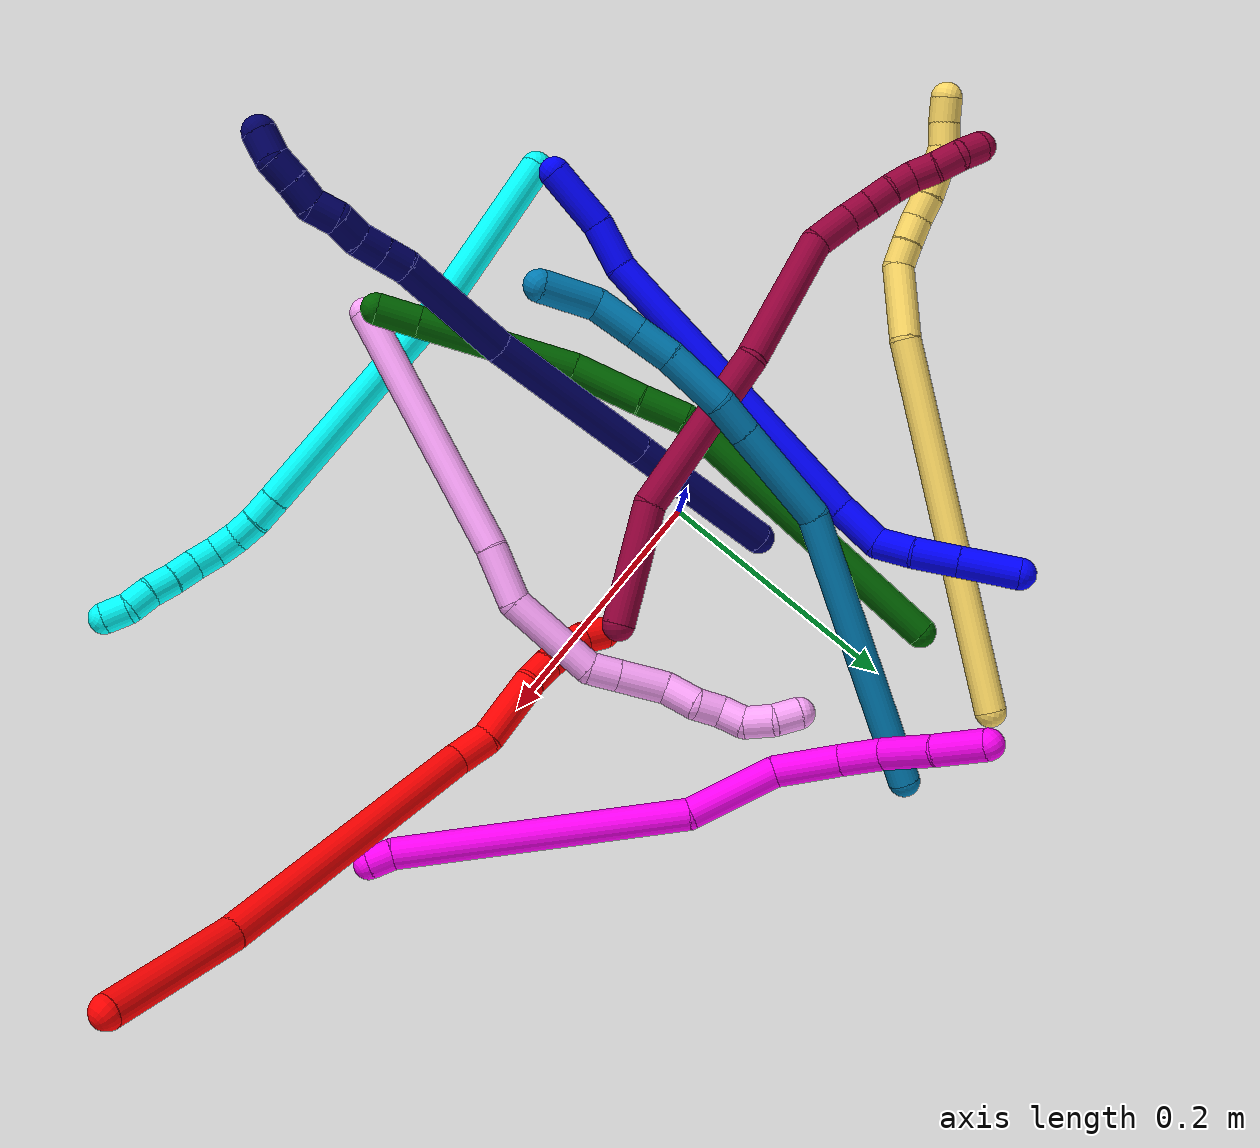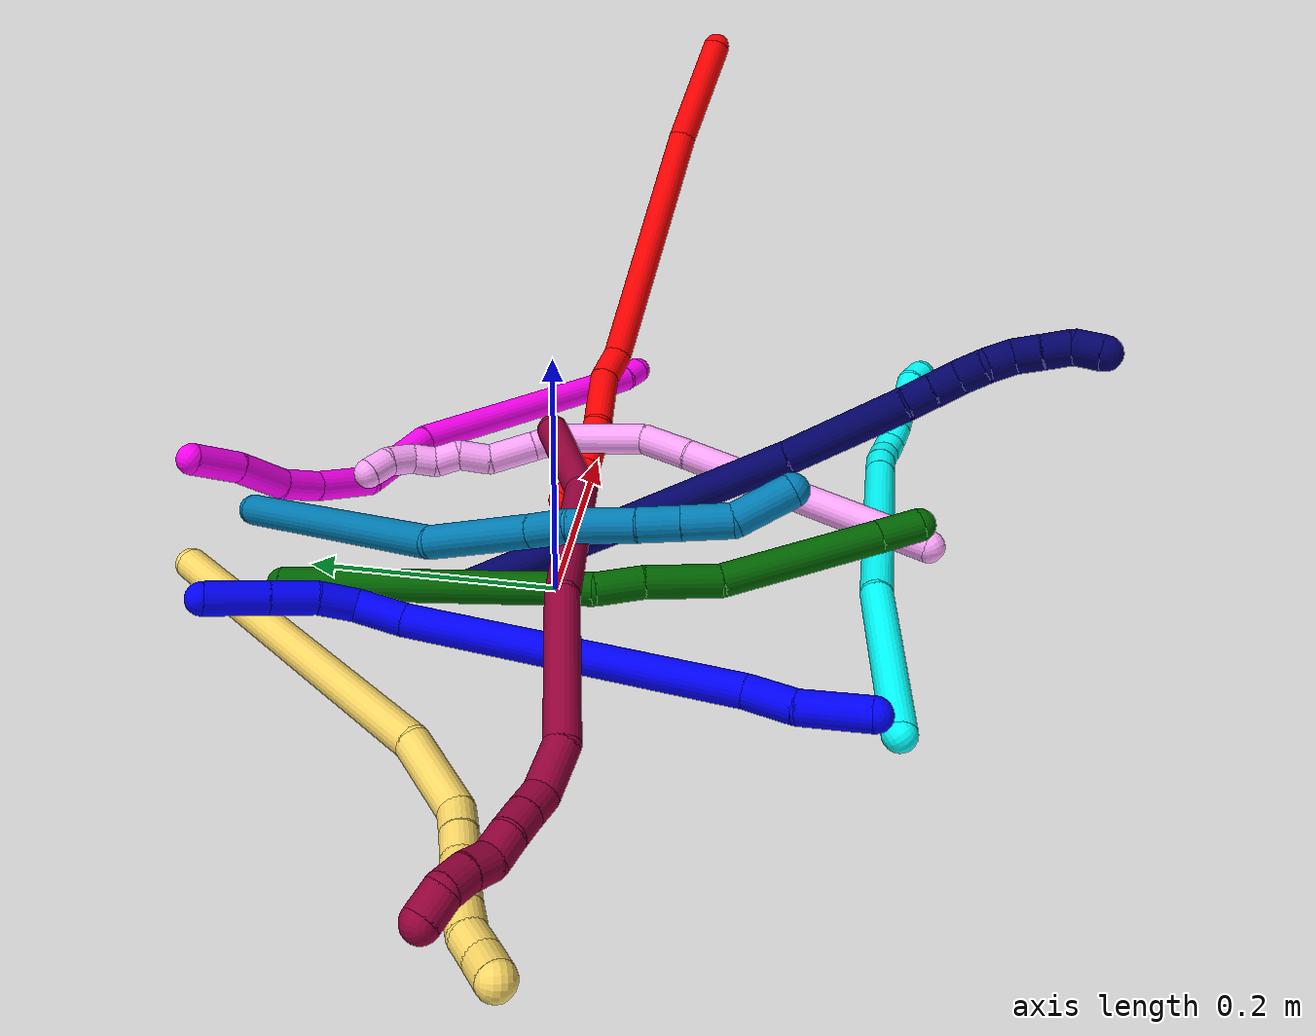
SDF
<sdf version="1.7">
 <world name="default">
  <plugin name="TubeGeneratorPlugin" filename="libtube_generator_plugin.so"/>
  <model name="photoneo_s_sensor">
   <static>1</static>
   <pose>0 0 2 1.57079 1.57079 3.14159</pose>
   <link name="link">
    <inertial><mass>0.1</mass></inertial>
    <sensor name="sensor" type="depth">
     <update_rate>30</update_rate>
     <camera>
      <horizontal_fov>1.22</horizontal_fov>
      <image><width>1920</width><height>1200</height><format>B8G8R8</format></image>
      <clip><near>0.1</near><far>2</far></clip>
      <depth_camera><output>points</output></depth_camera>
     </camera>
     <plugin name="camera_plugin" filename="libgazebo_ros_depth_camera.so">
      <baseline>0.2</baseline>
      <alwaysOn>1</alwaysOn>
      <updateRate>0.0</updateRate>
      <cameraName>camera_ir</cameraName>
      <imageTopicName>/camera/color/image_raw</imageTopicName>
      <cameraInfoTopicName>/camera/color/camera_info</cameraInfoTopicName>
      <depthImageTopicName>/camera/depth/image_raw</depthImageTopicName>
      <depthImageCameraInfoTopicName>/camera/depth/camera_info</depthImageCameraInfoTopicName>
      <pointCloudTopicName>/camera/depth/points</pointCloudTopicName>
      <frameName>fr_optical</frameName>
      <pointCloudCutoff>0.1</pointCloudCutoff>
      <pointCloudCutoffMax>2.0</pointCloudCutoffMax>
      <distortionK1>0</distortionK1>
      <distortionK2>0</distortionK2>
      <distortionK3>0</distortionK3>
      <distortionT1>0</distortionT1>
      <distortionT2>0</distortionT2>
      <CxPrime>0</CxPrime>
      <Cx>0</Cx>
      <Cy>0</Cy>
      <focalLength>0</focalLength>
      <hackBaseline>0</hackBaseline>
     </plugin>
    </sensor>
   </link>
  </model>
  <gravity>0 0 -9.8</gravity>
  <magnetic_field>6e-06 2.3e-05 -4.2e-05</magnetic_field>
  <atmosphere type="adiabatic"/>
  <physics name="default_physics" default="0" type="ode">
   <max_step_size>0.003</max_step_size>
   <real_time_factor>1</real_time_factor>
   <real_time_update_rate>1000</real_time_update_rate>
   <max_contacts>10000</max_contacts>
   <ode>
    <solver>
     <type>quick</type>
     <iters>100</iters>
     <sor>1.3</sor>
     <use_dynamic_moi_rescaling>0</use_dynamic_moi_rescaling>
    </solver>
    <constraints>
     <contact_max_correcting_vel>0</contact_max_correcting_vel>
     <contact_surface_layer>0.001</contact_surface_layer>
     <cfm>0</cfm>
     <erp>0.2</erp>
    </constraints>
   </ode>
  </physics>
  <scene><ambient>0.4 0.4 0.4 1</ambient><background>0.7 0.7 0.7 1</background><shadows>0</shadows></scene>
  <audio><device>default</device></audio>
  <spherical_coordinates>
   <surface_model>EARTH_WGS84</surface_model>
   <latitude_deg>0</latitude_deg>
   <longitude_deg>0</longitude_deg>
   <elevation>0</elevation>
   <heading_deg>0</heading_deg>
  </spherical_coordinates>
  <model name="bin">
   <static>1</static>
   <link name="bottom">
    <collision name="collision-bottom">
     <pose>0 0 -0.01 0 -0 0</pose>
     <geometry><box><size>0.8 0.6 0.02</size></box></geometry>
     <surface>
      <friction><ode><mu>100</mu><mu2>100</mu2></ode></friction>
      <contact><collide_bitmask>65535</collide_bitmask></contact>
     </surface>
    </collision>
   </link>
   <link name="west_wall">
    <collision name="collision-west_wall">
     <pose>-0.41 0 0.1 0 -0 0</pose>
     <geometry><box><size>0.02 0.6 0.2</size></box></geometry>
     <surface>
      <friction><ode><mu>100</mu><mu2>100</mu2></ode></friction>
      <contact><collide_bitmask>65535</collide_bitmask></contact>
     </surface>
    </collision>
   </link>
   <link name="east_wall">
    <collision name="collision-east_wall">
     <pose>0.41 0 0.1 0 -0 0</pose>
     <geometry><box><size>0.02 0.6 0.2</size></box></geometry>
     <surface>
      <friction><ode><mu>100</mu><mu2>100</mu2></ode></friction>
      <contact><collide_bitmask>65535</collide_bitmask></contact>
     </surface>
    </collision>
   </link>
   <link name="south_wall">
    <collision name="collision-south_wall">
     <pose>0 -0.31 0.1 0 -0 0</pose>
     <geometry><box><size>0.8 0.02 0.2</size></box></geometry>
     <surface>
      <friction><ode><mu>100</mu><mu2>100</mu2></ode></friction>
      <contact><collide_bitmask>65535</collide_bitmask></contact>
     </surface>
    </collision>
   </link>
   <link name="north_wall">
    <collision name="collision-north_wall">
     <pose>0 0.31 0.1 0 -0 0</pose>
     <geometry><box><size>0.8 0.02 0.2</size></box></geometry>
     <surface>
      <friction><ode><mu>100</mu><mu2>100</mu2></ode></friction>
      <contact><collide_bitmask>65535</collide_bitmask></contact>
     </surface>
    </collision>
   </link>
  </model>
  <model name="1">
   <static>0</static>
   <link name="1">
    <collision name="collision-cylinder-e_1_1_4">
     <pose>0.007492 0.023482 -0.009505 -1.9554 0.287556 -0.423145</pose>
     <geometry><cylinder><radius>0.0125</radius><length>0.052835</length></cylinder></geometry>
     <surface>
      <friction><ode><mu>1.16</mu><mu2>1.16</mu2><slip1>0</slip1><slip2>0</slip2></ode></friction>
      <contact><ode><kp>1e+06</kp><kd>1</kd><max_vel>0</max_vel><min_depth>0.001</min_depth></ode></contact>
     </surface>
    </collision>
    <visual name="visual-cylinder-e_1_1_4">
     <pose>0.007492 0.023482 -0.009505 -1.9554 0.287556 -0.423145</pose>
     <geometry><cylinder><radius>0.0125</radius><length>0.052835</length></cylinder></geometry>
     <material><ambient>0 0 1 1</ambient></material>
    </visual>
    <collision name="collision-cylinder-e_2_4_5">
     <pose>0.023475 0.061616 -0.02817 -2.12959 0.456728 -0.794299</pose>
     <geometry><cylinder><radius>0.0125</radius><length>0.038506</length></cylinder></geometry>
     <surface>
      <friction><ode><mu>1.16</mu><mu2>1.16</mu2><slip1>0</slip1><slip2>0</slip2></ode></friction>
      <contact><ode><kp>1e+06</kp><kd>1</kd><max_vel>0</max_vel><min_depth>0.001</min_depth></ode></contact>
     </surface>
    </collision>
    <visual name="visual-cylinder-e_2_4_5">
     <pose>0.023475 0.061616 -0.02817 -2.12959 0.456728 -0.794299</pose>
     <geometry><cylinder><radius>0.0125</radius><length>0.038506</length></cylinder></geometry>
     <material><ambient>0 0 1 1</ambient></material>
    </visual>
    <collision name="collision-cylinder-e_3_5_6">
     <pose>0.083991 0.189464 -0.069565 -1.84821 0.416204 -0.54543</pose>
     <geometry><cylinder><radius>0.0125</radius><length>0.257365</length></cylinder></geometry>
     <surface>
      <friction><ode><mu>1.16</mu><mu2>1.16</mu2><slip1>0</slip1><slip2>0</slip2></ode></friction>
      <contact><ode><kp>1e+06</kp><kd>1</kd><max_vel>0</max_vel><min_depth>0.001</min_depth></ode></contact>
     </surface>
    </collision>
    <visual name="visual-cylinder-e_3_5_6">
     <pose>0.083991 0.189464 -0.069565 -1.84821 0.416204 -0.54543</pose>
     <geometry><cylinder><radius>0.0125</radius><length>0.257365</length></cylinder></geometry>
     <material><ambient>0 0 1 1</ambient></material>
    </visual>
    <collision name="collision-cylinder-e_4_6_7">
     <pose>0.145712 0.319515 -0.103894 -1.69446 0.518707 -0.583555</pose>
     <geometry><cylinder><radius>0.0125</radius><length>0.039114</length></cylinder></geometry>
     <surface>
      <friction><ode><mu>1.16</mu><mu2>1.16</mu2><slip1>0</slip1><slip2>0</slip2></ode></friction>
      <contact><ode><kp>1e+06</kp><kd>1</kd><max_vel>0</max_vel><min_depth>0.001</min_depth></ode></contact>
     </surface>
    </collision>
    <visual name="visual-cylinder-e_4_6_7">
     <pose>0.145712 0.319515 -0.103894 -1.69446 0.518707 -0.583555</pose>
     <geometry><cylinder><radius>0.0125</radius><length>0.039114</length></cylinder></geometry>
     <material><ambient>0 0 1 1</ambient></material>
    </visual>
    <collision name="collision-cylinder-e_5_7_8">
     <pose>0.161009 0.348729 -0.100422 -1.14754 0.391835 -0.255142</pose>
     <geometry><cylinder><radius>0.0125</radius><length>0.029333</length></cylinder></geometry>
     <surface>
      <friction><ode><mu>1.16</mu><mu2>1.16</mu2><slip1>0</slip1><slip2>0</slip2></ode></friction>
      <contact><ode><kp>1e+06</kp><kd>1</kd><max_vel>0</max_vel><min_depth>0.001</min_depth></ode></contact>
     </surface>
    </collision>
    <visual name="visual-cylinder-e_5_7_8">
     <pose>0.161009 0.348729 -0.100422 -1.14754 0.391835 -0.255142</pose>
     <geometry><cylinder><radius>0.0125</radius><length>0.029333</length></cylinder></geometry>
     <material><ambient>0 0 1 1</ambient></material>
    </visual>
    <collision name="collision-cylinder-e_6_8_9">
     <pose>0.17022 0.377258 -0.088567 -1.19997 0.205182 -0.140631</pose>
     <geometry><cylinder><radius>0.0125</radius><length>0.035443</length></cylinder></geometry>
     <surface>
      <friction><ode><mu>1.16</mu><mu2>1.16</mu2><slip1>0</slip1><slip2>0</slip2></ode></friction>
      <contact><ode><kp>1e+06</kp><kd>1</kd><max_vel>0</max_vel><min_depth>0.001</min_depth></ode></contact>
     </surface>
    </collision>
    <visual name="visual-cylinder-e_6_8_9">
     <pose>0.17022 0.377258 -0.088567 -1.19997 0.205182 -0.140631</pose>
     <geometry><cylinder><radius>0.0125</radius><length>0.035443</length></cylinder></geometry>
     <material><ambient>0 0 1 1</ambient></material>
    </visual>
    <collision name="collision-cylinder-e_7_9_2">
     <pose>0.17866 0.415057 -0.073872 -1.20005 0.205181 -0.140642</pose>
     <geometry><cylinder><radius>0.0125</radius><length>0.047404</length></cylinder></geometry>
     <surface>
      <friction><ode><mu>1.16</mu><mu2>1.16</mu2><slip1>0</slip1><slip2>0</slip2></ode></friction>
      <contact><ode><kp>1e+06</kp><kd>1</kd><max_vel>0</max_vel><min_depth>0.001</min_depth></ode></contact>
     </surface>
    </collision>
    <visual name="visual-cylinder-e_7_9_2">
     <pose>0.17866 0.415057 -0.073872 -1.20005 0.205181 -0.140642</pose>
     <geometry><cylinder><radius>0.0125</radius><length>0.047404</length></cylinder></geometry>
     <material><ambient>0 0 1 1</ambient></material>
    </visual>
    <collision name="collision-sphere-2">
     <pose>0.183489 0.436685 -0.065465 0 -0 0</pose>
     <geometry><sphere><radius>0.0125</radius></sphere></geometry>
     <surface>
      <friction><ode><mu>1.16</mu><mu2>1.16</mu2><slip1>0</slip1><slip2>0</slip2></ode></friction>
      <contact><ode><kp>1e+06</kp><kd>1</kd><max_vel>0</max_vel><min_depth>0.001</min_depth></ode></contact>
     </surface>
    </collision>
    <visual name="visual-sphere-2">
     <pose>0.183489 0.436685 -0.065465 0 -0 0</pose>
     <geometry><sphere><radius>0.0125</radius></sphere></geometry>
     <material><ambient>0 0 1 1</ambient></material>
    </visual>
    <collision name="collision-sphere-9">
     <pose>0.173831 0.393429 -0.08228 0 -0 0</pose>
     <geometry><sphere><radius>0.0125</radius></sphere></geometry>
     <surface>
      <friction><ode><mu>1.16</mu><mu2>1.16</mu2><slip1>0</slip1><slip2>0</slip2></ode></friction>
      <contact><ode><kp>1e+06</kp><kd>1</kd><max_vel>0</max_vel><min_depth>0.001</min_depth></ode></contact>
     </surface>
    </collision>
    <visual name="visual-sphere-9">
     <pose>0.173831 0.393429 -0.08228 0 -0 0</pose>
     <geometry><sphere><radius>0.0125</radius></sphere></geometry>
     <material><ambient>0 0 1 1</ambient></material>
    </visual>
    <collision name="collision-sphere-4">
     <pose>0.014985 0.046965 -0.019009 0 -0 0</pose>
     <geometry><sphere><radius>0.0125</radius></sphere></geometry>
     <surface>
      <friction><ode><mu>1.16</mu><mu2>1.16</mu2><slip1>0</slip1><slip2>0</slip2></ode></friction>
      <contact><ode><kp>1e+06</kp><kd>1</kd><max_vel>0</max_vel><min_depth>0.001</min_depth></ode></contact>
     </surface>
    </collision>
    <visual name="visual-sphere-4">
     <pose>0.014985 0.046965 -0.019009 0 -0 0</pose>
     <geometry><sphere><radius>0.0125</radius></sphere></geometry>
     <material><ambient>0 0 1 1</ambient></material>
    </visual>
    <collision name="collision-sphere-1">
     <geometry><sphere><radius>0.0125</radius></sphere></geometry>
     <surface>
      <friction><ode><mu>1.16</mu><mu2>1.16</mu2><slip1>0</slip1><slip2>0</slip2></ode></friction>
      <contact><ode><kp>1e+06</kp><kd>1</kd><max_vel>0</max_vel><min_depth>0.001</min_depth></ode></contact>
     </surface>
    </collision>
    <visual name="visual-sphere-1">
     <geometry><sphere><radius>0.0125</radius></sphere></geometry>
     <material><ambient>0 0 1 1</ambient></material>
    </visual>
    <collision name="collision-sphere-8">
     <pose>0.16661 0.361088 -0.094854 0 -0 0</pose>
     <geometry><sphere><radius>0.0125</radius></sphere></geometry>
     <surface>
      <friction><ode><mu>1.16</mu><mu2>1.16</mu2><slip1>0</slip1><slip2>0</slip2></ode></friction>
      <contact><ode><kp>1e+06</kp><kd>1</kd><max_vel>0</max_vel><min_depth>0.001</min_depth></ode></contact>
     </surface>
    </collision>
    <visual name="visual-sphere-8">
     <pose>0.16661 0.361088 -0.094854 0 -0 0</pose>
     <geometry><sphere><radius>0.0125</radius></sphere></geometry>
     <material><ambient>0 0 1 1</ambient></material>
    </visual>
    <collision name="collision-sphere-5">
     <pose>0.031966 0.076267 -0.037331 0 -0 0</pose>
     <geometry><sphere><radius>0.0125</radius></sphere></geometry>
     <surface>
      <friction><ode><mu>1.16</mu><mu2>1.16</mu2><slip1>0</slip1><slip2>0</slip2></ode></friction>
      <contact><ode><kp>1e+06</kp><kd>1</kd><max_vel>0</max_vel><min_depth>0.001</min_depth></ode></contact>
     </surface>
    </collision>
    <visual name="visual-sphere-5">
     <pose>0.031966 0.076267 -0.037331 0 -0 0</pose>
     <geometry><sphere><radius>0.0125</radius></sphere></geometry>
     <material><ambient>0 0 1 1</ambient></material>
    </visual>
    <collision name="collision-sphere-6">
     <pose>0.136016 0.30266 -0.101799 0 -0 0</pose>
     <geometry><sphere><radius>0.0125</radius></sphere></geometry>
     <surface>
      <friction><ode><mu>1.16</mu><mu2>1.16</mu2><slip1>0</slip1><slip2>0</slip2></ode></friction>
      <contact><ode><kp>1e+06</kp><kd>1</kd><max_vel>0</max_vel><min_depth>0.001</min_depth></ode></contact>
     </surface>
    </collision>
    <visual name="visual-sphere-6">
     <pose>0.136016 0.30266 -0.101799 0 -0 0</pose>
     <geometry><sphere><radius>0.0125</radius></sphere></geometry>
     <material><ambient>0 0 1 1</ambient></material>
    </visual>
    <collision name="collision-sphere-7">
     <pose>0.155408 0.33637 -0.105989 0 -0 0</pose>
     <geometry><sphere><radius>0.0125</radius></sphere></geometry>
     <surface>
      <friction><ode><mu>1.16</mu><mu2>1.16</mu2><slip1>0</slip1><slip2>0</slip2></ode></friction>
      <contact><ode><kp>1e+06</kp><kd>1</kd><max_vel>0</max_vel><min_depth>0.001</min_depth></ode></contact>
     </surface>
    </collision>
    <visual name="visual-sphere-7">
     <pose>0.155408 0.33637 -0.105989 0 -0 0</pose>
     <geometry><sphere><radius>0.0125</radius></sphere></geometry>
     <material><ambient>0 0 1 1</ambient></material>
    </visual>
    <inertial>
     <pose>0.095682 0.216296 -0.066282 0 -0 0</pose>
     <mass>0.5</mass>
     <inertia>
      <ixx>0.000478</ixx>
      <ixy>0</ixy>
      <ixz>0</ixz>
      <iyy>-0.000702</iyy>
      <iyz>0</iyz>
      <izz>-0.001897</izz>
     </inertia>
    </inertial>
   </link>
   <pose>-0.143414 -0.243729 0.027978 -0.302015 -0.892091 0.547492</pose>
  </model>
  <model name="2">
   <static>0</static>
   <link name="2">
    <collision name="collision-cylinder-e_1_1_4">
     <pose>0.00484 0.016506 -0.048528 -2.81374 0.094148 -0.554908</pose>
     <geometry><cylinder><radius>0.0125</radius><length>0.102973</length></cylinder></geometry>
     <surface>
      <friction><ode><mu>1.16</mu><mu2>1.16</mu2><slip1>0</slip1><slip2>0</slip2></ode></friction>
      <contact><ode><kp>1e+06</kp><kd>1</kd><max_vel>0</max_vel><min_depth>0.001</min_depth></ode></contact>
     </surface>
    </collision>
    <visual name="visual-cylinder-e_1_1_4">
     <pose>0.00484 0.016506 -0.048528 -2.81374 0.094148 -0.554908</pose>
     <geometry><cylinder><radius>0.0125</radius><length>0.102973</length></cylinder></geometry>
     <material><ambient>1 0 0 1</ambient></material>
    </visual>
    <collision name="collision-cylinder-e_2_4_5">
     <pose>0.022089 0.058724 -0.209315 -2.91643 0.107332 -0.88711</pose>
     <geometry><cylinder><radius>0.0125</radius><length>0.231663</length></cylinder></geometry>
     <surface>
      <friction><ode><mu>1.16</mu><mu2>1.16</mu2><slip1>0</slip1><slip2>0</slip2></ode></friction>
      <contact><ode><kp>1e+06</kp><kd>1</kd><max_vel>0</max_vel><min_depth>0.001</min_depth></ode></contact>
     </surface>
    </collision>
    <visual name="visual-cylinder-e_2_4_5">
     <pose>0.022089 0.058724 -0.209315 -2.91643 0.107332 -0.88711</pose>
     <geometry><cylinder><radius>0.0125</radius><length>0.231663</length></cylinder></geometry>
     <material><ambient>1 0 0 1</ambient></material>
    </visual>
    <collision name="collision-cylinder-e_3_5_6">
     <pose>0.031321 0.085061 -0.336051 -3.09846 -0.215802 2.74849</pose>
     <geometry><cylinder><radius>0.0125</radius><length>0.029672</length></cylinder></geometry>
     <surface>
      <friction><ode><mu>1.16</mu><mu2>1.16</mu2><slip1>0</slip1><slip2>0</slip2></ode></friction>
      <contact><ode><kp>1e+06</kp><kd>1</kd><max_vel>0</max_vel><min_depth>0.001</min_depth></ode></contact>
     </surface>
    </collision>
    <visual name="visual-cylinder-e_3_5_6">
     <pose>0.031321 0.085061 -0.336051 -3.09846 -0.215802 2.74849</pose>
     <geometry><cylinder><radius>0.0125</radius><length>0.029672</length></cylinder></geometry>
     <material><ambient>1 0 0 1</ambient></material>
    </visual>
    <collision name="collision-cylinder-e_4_6_7">
     <pose>0.027352 0.07984 -0.377453 2.92778 -0.028747 -0.266311</pose>
     <geometry><cylinder><radius>0.0125</radius><length>0.055124</length></cylinder></geometry>
     <surface>
      <friction><ode><mu>1.16</mu><mu2>1.16</mu2><slip1>0</slip1><slip2>0</slip2></ode></friction>
      <contact><ode><kp>1e+06</kp><kd>1</kd><max_vel>0</max_vel><min_depth>0.001</min_depth></ode></contact>
     </surface>
    </collision>
    <visual name="visual-cylinder-e_4_6_7">
     <pose>0.027352 0.07984 -0.377453 2.92778 -0.028747 -0.266311</pose>
     <geometry><cylinder><radius>0.0125</radius><length>0.055124</length></cylinder></geometry>
     <material><ambient>1 0 0 1</ambient></material>
    </visual>
    <collision name="collision-cylinder-e_5_7_8">
     <pose>0.026969 0.07419 -0.41463 -3.12242 0.039956 -2.24683</pose>
     <geometry><cylinder><radius>0.0125</radius><length>0.020528</length></cylinder></geometry>
     <surface>
      <friction><ode><mu>1.16</mu><mu2>1.16</mu2><slip1>0</slip1><slip2>0</slip2></ode></friction>
      <contact><ode><kp>1e+06</kp><kd>1</kd><max_vel>0</max_vel><min_depth>0.001</min_depth></ode></contact>
     </surface>
    </collision>
    <visual name="visual-cylinder-e_5_7_8">
     <pose>0.026969 0.07419 -0.41463 -3.12242 0.039956 -2.24683</pose>
     <geometry><cylinder><radius>0.0125</radius><length>0.020528</length></cylinder></geometry>
     <material><ambient>1 0 0 1</ambient></material>
    </visual>
    <collision name="collision-cylinder-e_6_8_9">
     <pose>0.02762 0.075387 -0.434832 -3.04141 0.024067 -0.471158</pose>
     <geometry><cylinder><radius>0.0125</radius><length>0.02</length></cylinder></geometry>
     <surface>
      <friction><ode><mu>1.16</mu><mu2>1.16</mu2><slip1>0</slip1><slip2>0</slip2></ode></friction>
      <contact><ode><kp>1e+06</kp><kd>1</kd><max_vel>0</max_vel><min_depth>0.001</min_depth></ode></contact>
     </surface>
    </collision>
    <visual name="visual-cylinder-e_6_8_9">
     <pose>0.02762 0.075387 -0.434832 -3.04141 0.024067 -0.471158</pose>
     <geometry><cylinder><radius>0.0125</radius><length>0.02</length></cylinder></geometry>
     <material><ambient>1 0 0 1</ambient></material>
    </visual>
    <collision name="collision-cylinder-e_7_9_10">
     <pose>0.027354 0.077839 -0.454666 -2.99579 -0.050694 0.668282</pose>
     <geometry><cylinder><radius>0.0125</radius><length>0.020013</length></cylinder></geometry>
     <surface>
      <friction><ode><mu>1.16</mu><mu2>1.16</mu2><slip1>0</slip1><slip2>0</slip2></ode></friction>
      <contact><ode><kp>1e+06</kp><kd>1</kd><max_vel>0</max_vel><min_depth>0.001</min_depth></ode></contact>
     </surface>
    </collision>
    <visual name="visual-cylinder-e_7_9_10">
     <pose>0.027354 0.077839 -0.454666 -2.99579 -0.050694 0.668282</pose>
     <geometry><cylinder><radius>0.0125</radius><length>0.020013</length></cylinder></geometry>
     <material><ambient>1 0 0 1</ambient></material>
    </visual>
    <collision name="collision-cylinder-e_8_10_2">
     <pose>0.023722 0.082771 -0.473407 -2.76697 -0.317376 1.40243</pose>
     <geometry><cylinder><radius>0.0125</radius><length>0.020026</length></cylinder></geometry>
     <surface>
      <friction><ode><mu>1.16</mu><mu2>1.16</mu2><slip1>0</slip1><slip2>0</slip2></ode></friction>
      <contact><ode><kp>1e+06</kp><kd>1</kd><max_vel>0</max_vel><min_depth>0.001</min_depth></ode></contact>
     </surface>
    </collision>
    <visual name="visual-cylinder-e_8_10_2">
     <pose>0.023722 0.082771 -0.473407 -2.76697 -0.317376 1.40243</pose>
     <geometry><cylinder><radius>0.0125</radius><length>0.020026</length></cylinder></geometry>
     <material><ambient>1 0 0 1</ambient></material>
    </visual>
    <collision name="collision-sphere-2">
     <pose>0.020597 0.086252 -0.48226 0 -0 0</pose>
     <geometry><sphere><radius>0.0125</radius></sphere></geometry>
     <surface>
      <friction><ode><mu>1.16</mu><mu2>1.16</mu2><slip1>0</slip1><slip2>0</slip2></ode></friction>
      <contact><ode><kp>1e+06</kp><kd>1</kd><max_vel>0</max_vel><min_depth>0.001</min_depth></ode></contact>
     </surface>
    </collision>
    <visual name="visual-sphere-2">
     <pose>0.020597 0.086252 -0.48226 0 -0 0</pose>
     <geometry><sphere><radius>0.0125</radius></sphere></geometry>
     <material><ambient>1 0 0 1</ambient></material>
    </visual>
    <collision name="collision-sphere-10">
     <pose>0.026846 0.079291 -0.464554 0 -0 0</pose>
     <geometry><sphere><radius>0.0125</radius></sphere></geometry>
     <surface>
      <friction><ode><mu>1.16</mu><mu2>1.16</mu2><slip1>0</slip1><slip2>0</slip2></ode></friction>
      <contact><ode><kp>1e+06</kp><kd>1</kd><max_vel>0</max_vel><min_depth>0.001</min_depth></ode></contact>
     </surface>
    </collision>
    <visual name="visual-sphere-10">
     <pose>0.026846 0.079291 -0.464554 0 -0 0</pose>
     <geometry><sphere><radius>0.0125</radius></sphere></geometry>
     <material><ambient>1 0 0 1</ambient></material>
    </visual>
    <collision name="collision-sphere-9">
     <pose>0.027861 0.076387 -0.444779 0 -0 0</pose>
     <geometry><sphere><radius>0.0125</radius></sphere></geometry>
     <surface>
      <friction><ode><mu>1.16</mu><mu2>1.16</mu2><slip1>0</slip1><slip2>0</slip2></ode></friction>
      <contact><ode><kp>1e+06</kp><kd>1</kd><max_vel>0</max_vel><min_depth>0.001</min_depth></ode></contact>
     </surface>
    </collision>
    <visual name="visual-sphere-9">
     <pose>0.027861 0.076387 -0.444779 0 -0 0</pose>
     <geometry><sphere><radius>0.0125</radius></sphere></geometry>
     <material><ambient>1 0 0 1</ambient></material>
    </visual>
    <collision name="collision-sphere-4">
     <pose>0.00968 0.033012 -0.097057 0 -0 0</pose>
     <geometry><sphere><radius>0.0125</radius></sphere></geometry>
     <surface>
      <friction><ode><mu>1.16</mu><mu2>1.16</mu2><slip1>0</slip1><slip2>0</slip2></ode></friction>
      <contact><ode><kp>1e+06</kp><kd>1</kd><max_vel>0</max_vel><min_depth>0.001</min_depth></ode></contact>
     </surface>
    </collision>
    <visual name="visual-sphere-4">
     <pose>0.00968 0.033012 -0.097057 0 -0 0</pose>
     <geometry><sphere><radius>0.0125</radius></sphere></geometry>
     <material><ambient>1 0 0 1</ambient></material>
    </visual>
    <collision name="collision-sphere-1">
     <geometry><sphere><radius>0.0125</radius></sphere></geometry>
     <surface>
      <friction><ode><mu>1.16</mu><mu2>1.16</mu2><slip1>0</slip1><slip2>0</slip2></ode></friction>
      <contact><ode><kp>1e+06</kp><kd>1</kd><max_vel>0</max_vel><min_depth>0.001</min_depth></ode></contact>
     </surface>
    </collision>
    <visual name="visual-sphere-1">
     <geometry><sphere><radius>0.0125</radius></sphere></geometry>
     <material><ambient>1 0 0 1</ambient></material>
    </visual>
    <collision name="collision-sphere-8">
     <pose>0.027379 0.074387 -0.424884 0 -0 0</pose>
     <geometry><sphere><radius>0.0125</radius></sphere></geometry>
     <surface>
      <friction><ode><mu>1.16</mu><mu2>1.16</mu2><slip1>0</slip1><slip2>0</slip2></ode></friction>
      <contact><ode><kp>1e+06</kp><kd>1</kd><max_vel>0</max_vel><min_depth>0.001</min_depth></ode></contact>
     </surface>
    </collision>
    <visual name="visual-sphere-8">
     <pose>0.027379 0.074387 -0.424884 0 -0 0</pose>
     <geometry><sphere><radius>0.0125</radius></sphere></geometry>
     <material><ambient>1 0 0 1</ambient></material>
    </visual>
    <collision name="collision-sphere-5">
     <pose>0.034498 0.084436 -0.321573 0 -0 0</pose>
     <geometry><sphere><radius>0.0125</radius></sphere></geometry>
     <surface>
      <friction><ode><mu>1.16</mu><mu2>1.16</mu2><slip1>0</slip1><slip2>0</slip2></ode></friction>
      <contact><ode><kp>1e+06</kp><kd>1</kd><max_vel>0</max_vel><min_depth>0.001</min_depth></ode></contact>
     </surface>
    </collision>
    <visual name="visual-sphere-5">
     <pose>0.034498 0.084436 -0.321573 0 -0 0</pose>
     <geometry><sphere><radius>0.0125</radius></sphere></geometry>
     <material><ambient>1 0 0 1</ambient></material>
    </visual>
    <collision name="collision-sphere-6">
     <pose>0.028144 0.085685 -0.35053 0 -0 0</pose>
     <geometry><sphere><radius>0.0125</radius></sphere></geometry>
     <surface>
      <friction><ode><mu>1.16</mu><mu2>1.16</mu2><slip1>0</slip1><slip2>0</slip2></ode></friction>
      <contact><ode><kp>1e+06</kp><kd>1</kd><max_vel>0</max_vel><min_depth>0.001</min_depth></ode></contact>
     </surface>
    </collision>
    <visual name="visual-sphere-6">
     <pose>0.028144 0.085685 -0.35053 0 -0 0</pose>
     <geometry><sphere><radius>0.0125</radius></sphere></geometry>
     <material><ambient>1 0 0 1</ambient></material>
    </visual>
    <collision name="collision-sphere-7">
     <pose>0.026559 0.073994 -0.404376 0 -0 0</pose>
     <geometry><sphere><radius>0.0125</radius></sphere></geometry>
     <surface>
      <friction><ode><mu>1.16</mu><mu2>1.16</mu2><slip1>0</slip1><slip2>0</slip2></ode></friction>
      <contact><ode><kp>1e+06</kp><kd>1</kd><max_vel>0</max_vel><min_depth>0.001</min_depth></ode></contact>
     </surface>
    </collision>
    <visual name="visual-sphere-7">
     <pose>0.026559 0.073994 -0.404376 0 -0 0</pose>
     <geometry><sphere><radius>0.0125</radius></sphere></geometry>
     <material><ambient>1 0 0 1</ambient></material>
    </visual>
    <inertial>
     <pose>0.020362 0.05695 -0.240108 0 -0 0</pose>
     <mass>0.5</mass>
     <inertia>
      <ixx>-0.000105</ixx>
      <ixy>0</ixy>
      <ixz>0</ixz>
      <iyy>-0.001564</iyy>
      <iyz>0</iyz>
      <izz>-0.000417</izz>
     </inertia>
    </inertial>
   </link>
   <pose>0.491608 -0.068948 0.309786 -0.889886 0.692918 -1.18472</pose>
  </model>
  <model name="3">
   <static>0</static>
   <link name="3">
    <collision name="collision-cylinder-e_1_1_4">
     <pose>0.055555 0.033594 -0.019488 -2.09646 0.960689 -1.47074</pose>
     <geometry><cylinder><radius>0.0125</radius><length>0.135569</length></cylinder></geometry>
     <surface>
      <friction><ode><mu>1.16</mu><mu2>1.16</mu2><slip1>0</slip1><slip2>0</slip2></ode></friction>
      <contact><ode><kp>1e+06</kp><kd>1</kd><max_vel>0</max_vel><min_depth>0.001</min_depth></ode></contact>
     </surface>
    </collision>
    <visual name="visual-cylinder-e_1_1_4">
     <pose>0.055555 0.033594 -0.019488 -2.09646 0.960689 -1.47074</pose>
     <geometry><cylinder><radius>0.0125</radius><length>0.135569</length></cylinder></geometry>
     <material><ambient>0.003922 1 0.996078 1</ambient></material>
    </visual>
    <collision name="collision-cylinder-e_2_4_5">
     <pose>0.178439 0.135795 -0.068455 -1.97663 0.733731 -1.05616</pose>
     <geometry><cylinder><radius>0.0125</radius><length>0.201087</length></cylinder></geometry>
     <surface>
      <friction><ode><mu>1.16</mu><mu2>1.16</mu2><slip1>0</slip1><slip2>0</slip2></ode></friction>
      <contact><ode><kp>1e+06</kp><kd>1</kd><max_vel>0</max_vel><min_depth>0.001</min_depth></ode></contact>
     </surface>
    </collision>
    <visual name="visual-cylinder-e_2_4_5">
     <pose>0.178439 0.135795 -0.068455 -1.97663 0.733731 -1.05616</pose>
     <geometry><cylinder><radius>0.0125</radius><length>0.201087</length></cylinder></geometry>
     <material><ambient>0.003922 1 0.996078 1</ambient></material>
    </visual>
    <collision name="collision-cylinder-e_3_5_6">
     <pose>0.253281 0.212344 -0.101313 -1.97299 0.716233 -1.02995</pose>
     <geometry><cylinder><radius>0.0125</radius><length>0.022886</length></cylinder></geometry>
     <surface>
      <friction><ode><mu>1.16</mu><mu2>1.16</mu2><slip1>0</slip1><slip2>0</slip2></ode></friction>
      <contact><ode><kp>1e+06</kp><kd>1</kd><max_vel>0</max_vel><min_depth>0.001</min_depth></ode></contact>
     </surface>
    </collision>
    <visual name="visual-cylinder-e_3_5_6">
     <pose>0.253281 0.212344 -0.101313 -1.97299 0.716233 -1.02995</pose>
     <geometry><cylinder><radius>0.0125</radius><length>0.022886</length></cylinder></geometry>
     <material><ambient>0.003922 1 0.996078 1</ambient></material>
    </visual>
    <collision name="collision-cylinder-e_4_6_7">
     <pose>0.266072 0.228181 -0.108206 -1.98969 0.548301 -0.817364</pose>
     <geometry><cylinder><radius>0.0125</radius><length>0.020252</length></cylinder></geometry>
     <surface>
      <friction><ode><mu>1.16</mu><mu2>1.16</mu2><slip1>0</slip1><slip2>0</slip2></ode></friction>
      <contact><ode><kp>1e+06</kp><kd>1</kd><max_vel>0</max_vel><min_depth>0.001</min_depth></ode></contact>
     </surface>
    </collision>
    <visual name="visual-cylinder-e_4_6_7">
     <pose>0.266072 0.228181 -0.108206 -1.98969 0.548301 -0.817364</pose>
     <geometry><cylinder><radius>0.0125</radius><length>0.020252</length></cylinder></geometry>
     <material><ambient>0.003922 1 0.996078 1</ambient></material>
    </visual>
    <collision name="collision-cylinder-e_5_7_8">
     <pose>0.276881 0.242689 -0.116893 -2.23448 0.582609 -1.10292</pose>
     <geometry><cylinder><radius>0.0125</radius><length>0.020107</length></cylinder></geometry>
     <surface>
      <friction><ode><mu>1.16</mu><mu2>1.16</mu2><slip1>0</slip1><slip2>0</slip2></ode></friction>
      <contact><ode><kp>1e+06</kp><kd>1</kd><max_vel>0</max_vel><min_depth>0.001</min_depth></ode></contact>
     </surface>
    </collision>
    <visual name="visual-cylinder-e_5_7_8">
     <pose>0.276881 0.242689 -0.116893 -2.23448 0.582609 -1.10292</pose>
     <geometry><cylinder><radius>0.0125</radius><length>0.020107</length></cylinder></geometry>
     <material><ambient>0.003922 1 0.996078 1</ambient></material>
    </visual>
    <collision name="collision-cylinder-e_6_8_9">
     <pose>0.288618 0.253356 -0.128788 -2.59902 0.668832 -1.79152</pose>
     <geometry><cylinder><radius>0.0125</radius><length>0.020015</length></cylinder></geometry>
     <surface>
      <friction><ode><mu>1.16</mu><mu2>1.16</mu2><slip1>0</slip1><slip2>0</slip2></ode></friction>
      <contact><ode><kp>1e+06</kp><kd>1</kd><max_vel>0</max_vel><min_depth>0.001</min_depth></ode></contact>
     </surface>
    </collision>
    <visual name="visual-cylinder-e_6_8_9">
     <pose>0.288618 0.253356 -0.128788 -2.59902 0.668832 -1.79152</pose>
     <geometry><cylinder><radius>0.0125</radius><length>0.020015</length></cylinder></geometry>
     <material><ambient>0.003922 1 0.996078 1</ambient></material>
    </visual>
    <collision name="collision-cylinder-e_7_9_10">
     <pose>0.301709 0.260607 -0.142053 -2.68692 0.757525 -2.08852</pose>
     <geometry><cylinder><radius>0.0125</radius><length>0.020041</length></cylinder></geometry>
     <surface>
      <friction><ode><mu>1.16</mu><mu2>1.16</mu2><slip1>0</slip1><slip2>0</slip2></ode></friction>
      <contact><ode><kp>1e+06</kp><kd>1</kd><max_vel>0</max_vel><min_depth>0.001</min_depth></ode></contact>
     </surface>
    </collision>
    <visual name="visual-cylinder-e_7_9_10">
     <pose>0.301709 0.260607 -0.142053 -2.68692 0.757525 -2.08852</pose>
     <geometry><cylinder><radius>0.0125</radius><length>0.020041</length></cylinder></geometry>
     <material><ambient>0.003922 1 0.996078 1</ambient></material>
    </visual>
    <collision name="collision-cylinder-e_8_10_11">
     <pose>0.314767 0.267361 -0.155635 -2.67391 0.663993 -1.93238</pose>
     <geometry><cylinder><radius>0.0125</radius><length>0.020033</length></cylinder></geometry>
     <surface>
      <friction><ode><mu>1.16</mu><mu2>1.16</mu2><slip1>0</slip1><slip2>0</slip2></ode></friction>
      <contact><ode><kp>1e+06</kp><kd>1</kd><max_vel>0</max_vel><min_depth>0.001</min_depth></ode></contact>
     </surface>
    </collision>
    <visual name="visual-cylinder-e_8_10_11">
     <pose>0.314767 0.267361 -0.155635 -2.67391 0.663993 -1.93238</pose>
     <geometry><cylinder><radius>0.0125</radius><length>0.020033</length></cylinder></geometry>
     <material><ambient>0.003922 1 0.996078 1</ambient></material>
    </visual>
    <collision name="collision-cylinder-e_9_11_12">
     <pose>0.327937 0.275121 -0.16846 -2.51315 0.774528 -1.796</pose>
     <geometry><cylinder><radius>0.0125</radius><length>0.020008</length></cylinder></geometry>
     <surface>
      <friction><ode><mu>1.16</mu><mu2>1.16</mu2><slip1>0</slip1><slip2>0</slip2></ode></friction>
      <contact><ode><kp>1e+06</kp><kd>1</kd><max_vel>0</max_vel><min_depth>0.001</min_depth></ode></contact>
     </surface>
    </collision>
    <visual name="visual-cylinder-e_9_11_12">
     <pose>0.327937 0.275121 -0.16846 -2.51315 0.774528 -1.796</pose>
     <geometry><cylinder><radius>0.0125</radius><length>0.020008</length></cylinder></geometry>
     <material><ambient>0.003922 1 0.996078 1</ambient></material>
    </visual>
    <collision name="collision-cylinder-e_10_12_2">
     <pose>0.33864 0.285943 -0.180761 -2.34842 0.379715 -0.860444</pose>
     <geometry><cylinder><radius>0.0125</radius><length>0.020001</length></cylinder></geometry>
     <surface>
      <friction><ode><mu>1.16</mu><mu2>1.16</mu2><slip1>0</slip1><slip2>0</slip2></ode></friction>
      <contact><ode><kp>1e+06</kp><kd>1</kd><max_vel>0</max_vel><min_depth>0.001</min_depth></ode></contact>
     </surface>
    </collision>
    <visual name="visual-cylinder-e_10_12_2">
     <pose>0.33864 0.285943 -0.180761 -2.34842 0.379715 -0.860444</pose>
     <geometry><cylinder><radius>0.0125</radius><length>0.020001</length></cylinder></geometry>
     <material><ambient>0.003922 1 0.996078 1</ambient></material>
    </visual>
    <collision name="collision-sphere-2">
     <pose>0.342347 0.292561 -0.187277 0 -0 0</pose>
     <geometry><sphere><radius>0.0125</radius></sphere></geometry>
     <surface>
      <friction><ode><mu>1.16</mu><mu2>1.16</mu2><slip1>0</slip1><slip2>0</slip2></ode></friction>
      <contact><ode><kp>1e+06</kp><kd>1</kd><max_vel>0</max_vel><min_depth>0.001</min_depth></ode></contact>
     </surface>
    </collision>
    <visual name="visual-sphere-2">
     <pose>0.342347 0.292561 -0.187277 0 -0 0</pose>
     <geometry><sphere><radius>0.0125</radius></sphere></geometry>
     <material><ambient>0.003922 1 0.996078 1</ambient></material>
    </visual>
    <collision name="collision-sphere-12">
     <pose>0.334933 0.279324 -0.174244 0 -0 0</pose>
     <geometry><sphere><radius>0.0125</radius></sphere></geometry>
     <surface>
      <friction><ode><mu>1.16</mu><mu2>1.16</mu2><slip1>0</slip1><slip2>0</slip2></ode></friction>
      <contact><ode><kp>1e+06</kp><kd>1</kd><max_vel>0</max_vel><min_depth>0.001</min_depth></ode></contact>
     </surface>
    </collision>
    <visual name="visual-sphere-12">
     <pose>0.334933 0.279324 -0.174244 0 -0 0</pose>
     <geometry><sphere><radius>0.0125</radius></sphere></geometry>
     <material><ambient>0.003922 1 0.996078 1</ambient></material>
    </visual>
    <collision name="collision-sphere-11">
     <pose>0.32094 0.270917 -0.162676 0 -0 0</pose>
     <geometry><sphere><radius>0.0125</radius></sphere></geometry>
     <surface>
      <friction><ode><mu>1.16</mu><mu2>1.16</mu2><slip1>0</slip1><slip2>0</slip2></ode></friction>
      <contact><ode><kp>1e+06</kp><kd>1</kd><max_vel>0</max_vel><min_depth>0.001</min_depth></ode></contact>
     </surface>
    </collision>
    <visual name="visual-sphere-11">
     <pose>0.32094 0.270917 -0.162676 0 -0 0</pose>
     <geometry><sphere><radius>0.0125</radius></sphere></geometry>
     <material><ambient>0.003922 1 0.996078 1</ambient></material>
    </visual>
    <collision name="collision-sphere-10">
     <pose>0.308594 0.263805 -0.148593 0 -0 0</pose>
     <geometry><sphere><radius>0.0125</radius></sphere></geometry>
     <surface>
      <friction><ode><mu>1.16</mu><mu2>1.16</mu2><slip1>0</slip1><slip2>0</slip2></ode></friction>
      <contact><ode><kp>1e+06</kp><kd>1</kd><max_vel>0</max_vel><min_depth>0.001</min_depth></ode></contact>
     </surface>
    </collision>
    <visual name="visual-sphere-10">
     <pose>0.308594 0.263805 -0.148593 0 -0 0</pose>
     <geometry><sphere><radius>0.0125</radius></sphere></geometry>
     <material><ambient>0.003922 1 0.996078 1</ambient></material>
    </visual>
    <collision name="collision-sphere-9">
     <pose>0.294824 0.25741 -0.135512 0 -0 0</pose>
     <geometry><sphere><radius>0.0125</radius></sphere></geometry>
     <surface>
      <friction><ode><mu>1.16</mu><mu2>1.16</mu2><slip1>0</slip1><slip2>0</slip2></ode></friction>
      <contact><ode><kp>1e+06</kp><kd>1</kd><max_vel>0</max_vel><min_depth>0.001</min_depth></ode></contact>
     </surface>
    </collision>
    <visual name="visual-sphere-9">
     <pose>0.294824 0.25741 -0.135512 0 -0 0</pose>
     <geometry><sphere><radius>0.0125</radius></sphere></geometry>
     <material><ambient>0.003922 1 0.996078 1</ambient></material>
    </visual>
    <collision name="collision-sphere-4">
     <pose>0.111111 0.067188 -0.038976 0 -0 0</pose>
     <geometry><sphere><radius>0.0125</radius></sphere></geometry>
     <surface>
      <friction><ode><mu>1.16</mu><mu2>1.16</mu2><slip1>0</slip1><slip2>0</slip2></ode></friction>
      <contact><ode><kp>1e+06</kp><kd>1</kd><max_vel>0</max_vel><min_depth>0.001</min_depth></ode></contact>
     </surface>
    </collision>
    <visual name="visual-sphere-4">
     <pose>0.111111 0.067188 -0.038976 0 -0 0</pose>
     <geometry><sphere><radius>0.0125</radius></sphere></geometry>
     <material><ambient>0.003922 1 0.996078 1</ambient></material>
    </visual>
    <collision name="collision-sphere-1">
     <geometry><sphere><radius>0.0125</radius></sphere></geometry>
     <surface>
      <friction><ode><mu>1.16</mu><mu2>1.16</mu2><slip1>0</slip1><slip2>0</slip2></ode></friction>
      <contact><ode><kp>1e+06</kp><kd>1</kd><max_vel>0</max_vel><min_depth>0.001</min_depth></ode></contact>
     </surface>
    </collision>
    <visual name="visual-sphere-1">
     <geometry><sphere><radius>0.0125</radius></sphere></geometry>
     <material><ambient>0.003922 1 0.996078 1</ambient></material>
    </visual>
    <collision name="collision-sphere-8">
     <pose>0.282413 0.249302 -0.122064 0 -0 0</pose>
     <geometry><sphere><radius>0.0125</radius></sphere></geometry>
     <surface>
      <friction><ode><mu>1.16</mu><mu2>1.16</mu2><slip1>0</slip1><slip2>0</slip2></ode></friction>
      <contact><ode><kp>1e+06</kp><kd>1</kd><max_vel>0</max_vel><min_depth>0.001</min_depth></ode></contact>
     </surface>
    </collision>
    <visual name="visual-sphere-8">
     <pose>0.282413 0.249302 -0.122064 0 -0 0</pose>
     <geometry><sphere><radius>0.0125</radius></sphere></geometry>
     <material><ambient>0.003922 1 0.996078 1</ambient></material>
    </visual>
    <collision name="collision-sphere-5">
     <pose>0.245768 0.204402 -0.097934 0 -0 0</pose>
     <geometry><sphere><radius>0.0125</radius></sphere></geometry>
     <surface>
      <friction><ode><mu>1.16</mu><mu2>1.16</mu2><slip1>0</slip1><slip2>0</slip2></ode></friction>
      <contact><ode><kp>1e+06</kp><kd>1</kd><max_vel>0</max_vel><min_depth>0.001</min_depth></ode></contact>
     </surface>
    </collision>
    <visual name="visual-sphere-5">
     <pose>0.245768 0.204402 -0.097934 0 -0 0</pose>
     <geometry><sphere><radius>0.0125</radius></sphere></geometry>
     <material><ambient>0.003922 1 0.996078 1</ambient></material>
    </visual>
    <collision name="collision-sphere-6">
     <pose>0.260793 0.220287 -0.104691 0 -0 0</pose>
     <geometry><sphere><radius>0.0125</radius></sphere></geometry>
     <surface>
      <friction><ode><mu>1.16</mu><mu2>1.16</mu2><slip1>0</slip1><slip2>0</slip2></ode></friction>
      <contact><ode><kp>1e+06</kp><kd>1</kd><max_vel>0</max_vel><min_depth>0.001</min_depth></ode></contact>
     </surface>
    </collision>
    <visual name="visual-sphere-6">
     <pose>0.260793 0.220287 -0.104691 0 -0 0</pose>
     <geometry><sphere><radius>0.0125</radius></sphere></geometry>
     <material><ambient>0.003922 1 0.996078 1</ambient></material>
    </visual>
    <collision name="collision-sphere-7">
     <pose>0.27135 0.236076 -0.111721 0 -0 0</pose>
     <geometry><sphere><radius>0.0125</radius></sphere></geometry>
     <surface>
      <friction><ode><mu>1.16</mu><mu2>1.16</mu2><slip1>0</slip1><slip2>0</slip2></ode></friction>
      <contact><ode><kp>1e+06</kp><kd>1</kd><max_vel>0</max_vel><min_depth>0.001</min_depth></ode></contact>
     </surface>
    </collision>
    <visual name="visual-sphere-7">
     <pose>0.27135 0.236076 -0.111721 0 -0 0</pose>
     <geometry><sphere><radius>0.0125</radius></sphere></geometry>
     <material><ambient>0.003922 1 0.996078 1</ambient></material>
    </visual>
    <inertial>
     <pose>0.183259 0.146191 -0.077592 0 -0 0</pose>
     <mass>0.5</mass>
     <inertia>
      <ixx>-0.000282</ixx>
      <ixy>0</ixy>
      <ixz>0</ixz>
      <iyy>-0.000173</iyy>
      <iyz>0</iyz>
      <izz>-0.001235</izz>
     </inertia>
    </inertial>
   </link>
   <pose>-0.140548 -0.260982 0.011494 -2.22971 -0.410979 0.681465</pose>
  </model>
  <model name="4">
   <static>0</static>
   <link name="4">
    <collision name="collision-cylinder-e_1_1_4">
     <pose>0.001493 0.099975 -0.030166 -1.86385 0.014295 -0.019244</pose>
     <geometry><cylinder><radius>0.0125</radius><length>0.208875</length></cylinder></geometry>
     <surface>
      <friction><ode><mu>1.16</mu><mu2>1.16</mu2><slip1>0</slip1><slip2>0</slip2></ode></friction>
      <contact><ode><kp>1e+06</kp><kd>1</kd><max_vel>0</max_vel><min_depth>0.001</min_depth></ode></contact>
     </surface>
    </collision>
    <visual name="visual-cylinder-e_1_1_4">
     <pose>0.001493 0.099975 -0.030166 -1.86385 0.014295 -0.019244</pose>
     <geometry><cylinder><radius>0.0125</radius><length>0.208875</length></cylinder></geometry>
     <material><ambient>1 0.65098 0.996078 1</ambient></material>
    </visual>
    <collision name="collision-cylinder-e_2_4_5">
     <pose>0.005524 0.221767 -0.06496 -1.77982 0.113347 -0.139834</pose>
     <geometry><cylinder><radius>0.0125</radius><length>0.044892</length></cylinder></geometry>
     <surface>
      <friction><ode><mu>1.16</mu><mu2>1.16</mu2><slip1>0</slip1><slip2>0</slip2></ode></friction>
      <contact><ode><kp>1e+06</kp><kd>1</kd><max_vel>0</max_vel><min_depth>0.001</min_depth></ode></contact>
     </surface>
    </collision>
    <visual name="visual-cylinder-e_2_4_5">
     <pose>0.005524 0.221767 -0.06496 -1.77982 0.113347 -0.139834</pose>
     <geometry><cylinder><radius>0.0125</radius><length>0.044892</length></cylinder></geometry>
     <material><ambient>1 0.65098 0.996078 1</ambient></material>
    </visual>
    <collision name="collision-cylinder-e_3_5_6">
     <pose>0.0137 0.272589 -0.092636 -2.24223 0.150991 -0.310897</pose>
     <geometry><cylinder><radius>0.0125</radius><length>0.074947</length></cylinder></geometry>
     <surface>
      <friction><ode><mu>1.16</mu><mu2>1.16</mu2><slip1>0</slip1><slip2>0</slip2></ode></friction>
      <contact><ode><kp>1e+06</kp><kd>1</kd><max_vel>0</max_vel><min_depth>0.001</min_depth></ode></contact>
     </surface>
    </collision>
    <visual name="visual-cylinder-e_3_5_6">
     <pose>0.0137 0.272589 -0.092636 -2.24223 0.150991 -0.310897</pose>
     <geometry><cylinder><radius>0.0125</radius><length>0.074947</length></cylinder></geometry>
     <material><ambient>1 0.65098 0.996078 1</ambient></material>
    </visual>
    <collision name="collision-cylinder-e_4_6_7">
     <pose>0.021155 0.30626 -0.125963 -2.71555 0.159719 -0.70874</pose>
     <geometry><cylinder><radius>0.0125</radius><length>0.02287</length></cylinder></geometry>
     <surface>
      <friction><ode><mu>1.16</mu><mu2>1.16</mu2><slip1>0</slip1><slip2>0</slip2></ode></friction>
      <contact><ode><kp>1e+06</kp><kd>1</kd><max_vel>0</max_vel><min_depth>0.001</min_depth></ode></contact>
     </surface>
    </collision>
    <visual name="visual-cylinder-e_4_6_7">
     <pose>0.021155 0.30626 -0.125963 -2.71555 0.159719 -0.70874</pose>
     <geometry><cylinder><radius>0.0125</radius><length>0.02287</length></cylinder></geometry>
     <material><ambient>1 0.65098 0.996078 1</ambient></material>
    </visual>
    <collision name="collision-cylinder-e_5_7_8">
     <pose>0.025979 0.318769 -0.153702 -2.71936 0.155729 -0.698303</pose>
     <geometry><cylinder><radius>0.0125</radius><length>0.038748</length></cylinder></geometry>
     <surface>
      <friction><ode><mu>1.16</mu><mu2>1.16</mu2><slip1>0</slip1><slip2>0</slip2></ode></friction>
      <contact><ode><kp>1e+06</kp><kd>1</kd><max_vel>0</max_vel><min_depth>0.001</min_depth></ode></contact>
     </surface>
    </collision>
    <visual name="visual-cylinder-e_5_7_8">
     <pose>0.025979 0.318769 -0.153702 -2.71936 0.155729 -0.698303</pose>
     <geometry><cylinder><radius>0.0125</radius><length>0.038748</length></cylinder></geometry>
     <material><ambient>1 0.65098 0.996078 1</ambient></material>
    </visual>
    <collision name="collision-cylinder-e_6_8_9">
     <pose>0.026791 0.33522 -0.180863 -2.41588 -0.167437 0.435047</pose>
     <geometry><cylinder><radius>0.0125</radius><length>0.026309</length></cylinder></geometry>
     <surface>
      <friction><ode><mu>1.16</mu><mu2>1.16</mu2><slip1>0</slip1><slip2>0</slip2></ode></friction>
      <contact><ode><kp>1e+06</kp><kd>1</kd><max_vel>0</max_vel><min_depth>0.001</min_depth></ode></contact>
     </surface>
    </collision>
    <visual name="visual-cylinder-e_6_8_9">
     <pose>0.026791 0.33522 -0.180863 -2.41588 -0.167437 0.435047</pose>
     <geometry><cylinder><radius>0.0125</radius><length>0.026309</length></cylinder></geometry>
     <material><ambient>1 0.65098 0.996078 1</ambient></material>
    </visual>
    <collision name="collision-cylinder-e_7_9_10">
     <pose>0.026542 0.348223 -0.199475 -2.68333 0.193094 -0.787165</pose>
     <geometry><cylinder><radius>0.0125</radius><length>0.020247</length></cylinder></geometry>
     <surface>
      <friction><ode><mu>1.16</mu><mu2>1.16</mu2><slip1>0</slip1><slip2>0</slip2></ode></friction>
      <contact><ode><kp>1e+06</kp><kd>1</kd><max_vel>0</max_vel><min_depth>0.001</min_depth></ode></contact>
     </surface>
    </collision>
    <visual name="visual-cylinder-e_7_9_10">
     <pose>0.026542 0.348223 -0.199475 -2.68333 0.193094 -0.787165</pose>
     <geometry><cylinder><radius>0.0125</radius><length>0.020247</length></cylinder></geometry>
     <material><ambient>1 0.65098 0.996078 1</ambient></material>
    </visual>
    <collision name="collision-cylinder-e_8_10_11">
     <pose>0.02641 0.358787 -0.216149 -2.47022 -0.206222 0.576649</pose>
     <geometry><cylinder><radius>0.0125</radius><length>0.02026</length></cylinder></geometry>
     <surface>
      <friction><ode><mu>1.16</mu><mu2>1.16</mu2><slip1>0</slip1><slip2>0</slip2></ode></friction>
      <contact><ode><kp>1e+06</kp><kd>1</kd><max_vel>0</max_vel><min_depth>0.001</min_depth></ode></contact>
     </surface>
    </collision>
    <visual name="visual-cylinder-e_8_10_11">
     <pose>0.02641 0.358787 -0.216149 -2.47022 -0.206222 0.576649</pose>
     <geometry><cylinder><radius>0.0125</radius><length>0.02026</length></cylinder></geometry>
     <material><ambient>1 0.65098 0.996078 1</ambient></material>
    </visual>
    <collision name="collision-cylinder-e_9_11_12">
     <pose>0.021405 0.366564 -0.234828 -2.99521 -0.259617 2.11805</pose>
     <geometry><cylinder><radius>0.0125</radius><length>0.022833</length></cylinder></geometry>
     <surface>
      <friction><ode><mu>1.16</mu><mu2>1.16</mu2><slip1>0</slip1><slip2>0</slip2></ode></friction>
      <contact><ode><kp>1e+06</kp><kd>1</kd><max_vel>0</max_vel><min_depth>0.001</min_depth></ode></contact>
     </surface>
    </collision>
    <visual name="visual-cylinder-e_9_11_12">
     <pose>0.021405 0.366564 -0.234828 -2.99521 -0.259617 2.11805</pose>
     <geometry><cylinder><radius>0.0125</radius><length>0.022833</length></cylinder></geometry>
     <material><ambient>1 0.65098 0.996078 1</ambient></material>
    </visual>
    <collision name="collision-cylinder-e_10_12_2">
     <pose>0.018837 0.367336 -0.255712 3.05778 0.036167 0.814435</pose>
     <geometry><cylinder><radius>0.0125</radius><length>0.020019</length></cylinder></geometry>
     <surface>
      <friction><ode><mu>1.16</mu><mu2>1.16</mu2><slip1>0</slip1><slip2>0</slip2></ode></friction>
      <contact><ode><kp>1e+06</kp><kd>1</kd><max_vel>0</max_vel><min_depth>0.001</min_depth></ode></contact>
     </surface>
    </collision>
    <visual name="visual-cylinder-e_10_12_2">
     <pose>0.018837 0.367336 -0.255712 3.05778 0.036167 0.814435</pose>
     <geometry><cylinder><radius>0.0125</radius><length>0.020019</length></cylinder></geometry>
     <material><ambient>1 0.65098 0.996078 1</ambient></material>
    </visual>
    <collision name="collision-sphere-2">
     <pose>0.019199 0.366499 -0.26568 0 -0 0</pose>
     <geometry><sphere><radius>0.0125</radius></sphere></geometry>
     <surface>
      <friction><ode><mu>1.16</mu><mu2>1.16</mu2><slip1>0</slip1><slip2>0</slip2></ode></friction>
      <contact><ode><kp>1e+06</kp><kd>1</kd><max_vel>0</max_vel><min_depth>0.001</min_depth></ode></contact>
     </surface>
    </collision>
    <visual name="visual-sphere-2">
     <pose>0.019199 0.366499 -0.26568 0 -0 0</pose>
     <geometry><sphere><radius>0.0125</radius></sphere></geometry>
     <material><ambient>1 0.65098 0.996078 1</ambient></material>
    </visual>
    <collision name="collision-sphere-12">
     <pose>0.018475 0.368173 -0.245744 0 -0 0</pose>
     <geometry><sphere><radius>0.0125</radius></sphere></geometry>
     <surface>
      <friction><ode><mu>1.16</mu><mu2>1.16</mu2><slip1>0</slip1><slip2>0</slip2></ode></friction>
      <contact><ode><kp>1e+06</kp><kd>1</kd><max_vel>0</max_vel><min_depth>0.001</min_depth></ode></contact>
     </surface>
    </collision>
    <visual name="visual-sphere-12">
     <pose>0.018475 0.368173 -0.245744 0 -0 0</pose>
     <geometry><sphere><radius>0.0125</radius></sphere></geometry>
     <material><ambient>1 0.65098 0.996078 1</ambient></material>
    </visual>
    <collision name="collision-sphere-11">
     <pose>0.024336 0.364954 -0.223912 0 -0 0</pose>
     <geometry><sphere><radius>0.0125</radius></sphere></geometry>
     <surface>
      <friction><ode><mu>1.16</mu><mu2>1.16</mu2><slip1>0</slip1><slip2>0</slip2></ode></friction>
      <contact><ode><kp>1e+06</kp><kd>1</kd><max_vel>0</max_vel><min_depth>0.001</min_depth></ode></contact>
     </surface>
    </collision>
    <visual name="visual-sphere-11">
     <pose>0.024336 0.364954 -0.223912 0 -0 0</pose>
     <geometry><sphere><radius>0.0125</radius></sphere></geometry>
     <material><ambient>1 0.65098 0.996078 1</ambient></material>
    </visual>
    <collision name="collision-sphere-10">
     <pose>0.028485 0.352619 -0.208386 0 -0 0</pose>
     <geometry><sphere><radius>0.0125</radius></sphere></geometry>
     <surface>
      <friction><ode><mu>1.16</mu><mu2>1.16</mu2><slip1>0</slip1><slip2>0</slip2></ode></friction>
      <contact><ode><kp>1e+06</kp><kd>1</kd><max_vel>0</max_vel><min_depth>0.001</min_depth></ode></contact>
     </surface>
    </collision>
    <visual name="visual-sphere-10">
     <pose>0.028485 0.352619 -0.208386 0 -0 0</pose>
     <geometry><sphere><radius>0.0125</radius></sphere></geometry>
     <material><ambient>1 0.65098 0.996078 1</ambient></material>
    </visual>
    <collision name="collision-sphere-9">
     <pose>0.024599 0.343828 -0.190565 0 -0 0</pose>
     <geometry><sphere><radius>0.0125</radius></sphere></geometry>
     <surface>
      <friction><ode><mu>1.16</mu><mu2>1.16</mu2><slip1>0</slip1><slip2>0</slip2></ode></friction>
      <contact><ode><kp>1e+06</kp><kd>1</kd><max_vel>0</max_vel><min_depth>0.001</min_depth></ode></contact>
     </surface>
    </collision>
    <visual name="visual-sphere-9">
     <pose>0.024599 0.343828 -0.190565 0 -0 0</pose>
     <geometry><sphere><radius>0.0125</radius></sphere></geometry>
     <material><ambient>1 0.65098 0.996078 1</ambient></material>
    </visual>
    <collision name="collision-sphere-4">
     <pose>0.002986 0.19995 -0.060332 0 -0 0</pose>
     <geometry><sphere><radius>0.0125</radius></sphere></geometry>
     <surface>
      <friction><ode><mu>1.16</mu><mu2>1.16</mu2><slip1>0</slip1><slip2>0</slip2></ode></friction>
      <contact><ode><kp>1e+06</kp><kd>1</kd><max_vel>0</max_vel><min_depth>0.001</min_depth></ode></contact>
     </surface>
    </collision>
    <visual name="visual-sphere-4">
     <pose>0.002986 0.19995 -0.060332 0 -0 0</pose>
     <geometry><sphere><radius>0.0125</radius></sphere></geometry>
     <material><ambient>1 0.65098 0.996078 1</ambient></material>
    </visual>
    <collision name="collision-sphere-1">
     <geometry><sphere><radius>0.0125</radius></sphere></geometry>
     <surface>
      <friction><ode><mu>1.16</mu><mu2>1.16</mu2><slip1>0</slip1><slip2>0</slip2></ode></friction>
      <contact><ode><kp>1e+06</kp><kd>1</kd><max_vel>0</max_vel><min_depth>0.001</min_depth></ode></contact>
     </surface>
    </collision>
    <visual name="visual-sphere-1">
     <geometry><sphere><radius>0.0125</radius></sphere></geometry>
     <material><ambient>1 0.65098 0.996078 1</ambient></material>
    </visual>
    <collision name="collision-sphere-8">
     <pose>0.028984 0.326612 -0.171161 0 -0 0</pose>
     <geometry><sphere><radius>0.0125</radius></sphere></geometry>
     <surface>
      <friction><ode><mu>1.16</mu><mu2>1.16</mu2><slip1>0</slip1><slip2>0</slip2></ode></friction>
      <contact><ode><kp>1e+06</kp><kd>1</kd><max_vel>0</max_vel><min_depth>0.001</min_depth></ode></contact>
     </surface>
    </collision>
    <visual name="visual-sphere-8">
     <pose>0.028984 0.326612 -0.171161 0 -0 0</pose>
     <geometry><sphere><radius>0.0125</radius></sphere></geometry>
     <material><ambient>1 0.65098 0.996078 1</ambient></material>
    </visual>
    <collision name="collision-sphere-5">
     <pose>0.008063 0.243584 -0.069588 0 -0 0</pose>
     <geometry><sphere><radius>0.0125</radius></sphere></geometry>
     <surface>
      <friction><ode><mu>1.16</mu><mu2>1.16</mu2><slip1>0</slip1><slip2>0</slip2></ode></friction>
      <contact><ode><kp>1e+06</kp><kd>1</kd><max_vel>0</max_vel><min_depth>0.001</min_depth></ode></contact>
     </surface>
    </collision>
    <visual name="visual-sphere-5">
     <pose>0.008063 0.243584 -0.069588 0 -0 0</pose>
     <geometry><sphere><radius>0.0125</radius></sphere></geometry>
     <material><ambient>1 0.65098 0.996078 1</ambient></material>
    </visual>
    <collision name="collision-sphere-6">
     <pose>0.019337 0.301594 -0.115683 0 -0 0</pose>
     <geometry><sphere><radius>0.0125</radius></sphere></geometry>
     <surface>
      <friction><ode><mu>1.16</mu><mu2>1.16</mu2><slip1>0</slip1><slip2>0</slip2></ode></friction>
      <contact><ode><kp>1e+06</kp><kd>1</kd><max_vel>0</max_vel><min_depth>0.001</min_depth></ode></contact>
     </surface>
    </collision>
    <visual name="visual-sphere-6">
     <pose>0.019337 0.301594 -0.115683 0 -0 0</pose>
     <geometry><sphere><radius>0.0125</radius></sphere></geometry>
     <material><ambient>1 0.65098 0.996078 1</ambient></material>
    </visual>
    <collision name="collision-sphere-7">
     <pose>0.022974 0.310926 -0.136244 0 -0 0</pose>
     <geometry><sphere><radius>0.0125</radius></sphere></geometry>
     <surface>
      <friction><ode><mu>1.16</mu><mu2>1.16</mu2><slip1>0</slip1><slip2>0</slip2></ode></friction>
      <contact><ode><kp>1e+06</kp><kd>1</kd><max_vel>0</max_vel><min_depth>0.001</min_depth></ode></contact>
     </surface>
    </collision>
    <visual name="visual-sphere-7">
     <pose>0.022974 0.310926 -0.136244 0 -0 0</pose>
     <geometry><sphere><radius>0.0125</radius></sphere></geometry>
     <material><ambient>1 0.65098 0.996078 1</ambient></material>
    </visual>
    <inertial>
     <pose>0.01144 0.218971 -0.097307 0 -0 0</pose>
     <mass>0.5</mass>
     <inertia>
      <ixx>0.000795</ixx>
      <ixy>0</ixy>
      <ixz>0</ixz>
      <iyy>-0.000254</iyy>
      <iyz>0</iyz>
      <izz>-0.000819</izz>
     </inertia>
    </inertial>
   </link>
   <pose>0.037466 -0.283077 0.046355 0.951464 1.41456 0.265299</pose>
  </model>
  <model name="5">
   <static>0</static>
   <link name="5">
    <collision name="collision-cylinder-e_1_1_4">
     <pose>-0.055573 -0.120719 0.066983 1.06423 -0.382691 -0.227122</pose>
     <geometry><cylinder><radius>0.0125</radius><length>0.297645</length></cylinder></geometry>
     <surface>
      <friction><ode><mu>1.16</mu><mu2>1.16</mu2><slip1>0</slip1><slip2>0</slip2></ode></friction>
      <contact><ode><kp>1e+06</kp><kd>1</kd><max_vel>0</max_vel><min_depth>0.001</min_depth></ode></contact>
     </surface>
    </collision>
    <visual name="visual-cylinder-e_1_1_4">
     <pose>-0.055573 -0.120719 0.066983 1.06423 -0.382691 -0.227122</pose>
     <geometry><cylinder><radius>0.0125</radius><length>0.297645</length></cylinder></geometry>
     <material><ambient>1 0.858824 0.4 1</ambient></material>
    </visual>
    <collision name="collision-cylinder-e_2_4_5">
     <pose>-0.115953 -0.269705 0.144463 1.2152 -0.158091 -0.110048</pose>
     <geometry><cylinder><radius>0.0125</radius><length>0.061067</length></cylinder></geometry>
     <surface>
      <friction><ode><mu>1.16</mu><mu2>1.16</mu2><slip1>0</slip1><slip2>0</slip2></ode></friction>
      <contact><ode><kp>1e+06</kp><kd>1</kd><max_vel>0</max_vel><min_depth>0.001</min_depth></ode></contact>
     </surface>
    </collision>
    <visual name="visual-cylinder-e_2_4_5">
     <pose>-0.115953 -0.269705 0.144463 1.2152 -0.158091 -0.110048</pose>
     <geometry><cylinder><radius>0.0125</radius><length>0.061067</length></cylinder></geometry>
     <material><ambient>1 0.858824 0.4 1</ambient></material>
    </visual>
    <collision name="collision-cylinder-e_3_5_6">
     <pose>-0.12371 -0.307651 0.15406 1.66359 -0.294641 -0.32286</pose>
     <geometry><cylinder><radius>0.0125</radius><length>0.020319</length></cylinder></geometry>
     <surface>
      <friction><ode><mu>1.16</mu><mu2>1.16</mu2><slip1>0</slip1><slip2>0</slip2></ode></friction>
      <contact><ode><kp>1e+06</kp><kd>1</kd><max_vel>0</max_vel><min_depth>0.001</min_depth></ode></contact>
     </surface>
    </collision>
    <visual name="visual-cylinder-e_3_5_6">
     <pose>-0.12371 -0.307651 0.15406 1.66359 -0.294641 -0.32286</pose>
     <geometry><cylinder><radius>0.0125</radius><length>0.020319</length></cylinder></geometry>
     <material><ambient>1 0.858824 0.4 1</ambient></material>
    </visual>
    <collision name="collision-cylinder-e_4_6_7">
     <pose>-0.128981 -0.327479 0.151945 1.68987 -0.223206 -0.251222</pose>
     <geometry><cylinder><radius>0.0125</radius><length>0.020961</length></cylinder></geometry>
     <surface>
      <friction><ode><mu>1.16</mu><mu2>1.16</mu2><slip1>0</slip1><slip2>0</slip2></ode></friction>
      <contact><ode><kp>1e+06</kp><kd>1</kd><max_vel>0</max_vel><min_depth>0.001</min_depth></ode></contact>
     </surface>
    </collision>
    <visual name="visual-cylinder-e_4_6_7">
     <pose>-0.128981 -0.327479 0.151945 1.68987 -0.223206 -0.251222</pose>
     <geometry><cylinder><radius>0.0125</radius><length>0.020961</length></cylinder></geometry>
     <material><ambient>1 0.858824 0.4 1</ambient></material>
    </visual>
    <collision name="collision-cylinder-e_5_7_8">
     <pose>-0.134505 -0.346888 0.148725 1.78411 -0.326119 -0.402423</pose>
     <geometry><cylinder><radius>0.0125</radius><length>0.020007</length></cylinder></geometry>
     <surface>
      <friction><ode><mu>1.16</mu><mu2>1.16</mu2><slip1>0</slip1><slip2>0</slip2></ode></friction>
      <contact><ode><kp>1e+06</kp><kd>1</kd><max_vel>0</max_vel><min_depth>0.001</min_depth></ode></contact>
     </surface>
    </collision>
    <visual name="visual-cylinder-e_5_7_8">
     <pose>-0.134505 -0.346888 0.148725 1.78411 -0.326119 -0.402423</pose>
     <geometry><cylinder><radius>0.0125</radius><length>0.020007</length></cylinder></geometry>
     <material><ambient>1 0.858824 0.4 1</ambient></material>
    </visual>
    <collision name="collision-cylinder-e_6_8_9">
     <pose>-0.140662 -0.365664 0.145845 1.6624 -0.299657 -0.327953</pose>
     <geometry><cylinder><radius>0.0125</radius><length>0.020001</length></cylinder></geometry>
     <surface>
      <friction><ode><mu>1.16</mu><mu2>1.16</mu2><slip1>0</slip1><slip2>0</slip2></ode></friction>
      <contact><ode><kp>1e+06</kp><kd>1</kd><max_vel>0</max_vel><min_depth>0.001</min_depth></ode></contact>
     </surface>
    </collision>
    <visual name="visual-cylinder-e_6_8_9">
     <pose>-0.140662 -0.365664 0.145845 1.6624 -0.299657 -0.327953</pose>
     <geometry><cylinder><radius>0.0125</radius><length>0.020001</length></cylinder></geometry>
     <material><ambient>1 0.858824 0.4 1</ambient></material>
    </visual>
    <collision name="collision-cylinder-e_7_9_10">
     <pose>-0.146819 -0.384643 0.14455 1.61525 -0.326193 -0.340745</pose>
     <geometry><cylinder><radius>0.0125</radius><length>0.02</length></cylinder></geometry>
     <surface>
      <friction><ode><mu>1.16</mu><mu2>1.16</mu2><slip1>0</slip1><slip2>0</slip2></ode></friction>
      <contact><ode><kp>1e+06</kp><kd>1</kd><max_vel>0</max_vel><min_depth>0.001</min_depth></ode></contact>
     </surface>
    </collision>
    <visual name="visual-cylinder-e_7_9_10">
     <pose>-0.146819 -0.384643 0.14455 1.61525 -0.326193 -0.340745</pose>
     <geometry><cylinder><radius>0.0125</radius><length>0.02</length></cylinder></geometry>
     <material><ambient>1 0.858824 0.4 1</ambient></material>
    </visual>
    <collision name="collision-cylinder-e_8_10_11">
     <pose>-0.15408 -0.40296 0.146399 1.31983 -0.417688 -0.325989</pose>
     <geometry><cylinder><radius>0.0125</radius><length>0.02</length></cylinder></geometry>
     <surface>
      <friction><ode><mu>1.16</mu><mu2>1.16</mu2><slip1>0</slip1><slip2>0</slip2></ode></friction>
      <contact><ode><kp>1e+06</kp><kd>1</kd><max_vel>0</max_vel><min_depth>0.001</min_depth></ode></contact>
     </surface>
    </collision>
    <visual name="visual-cylinder-e_8_10_11">
     <pose>-0.15408 -0.40296 0.146399 1.31983 -0.417688 -0.325989</pose>
     <geometry><cylinder><radius>0.0125</radius><length>0.02</length></cylinder></geometry>
     <material><ambient>1 0.858824 0.4 1</ambient></material>
    </visual>
    <collision name="collision-cylinder-e_9_11_2">
     <pose>-0.163234 -0.420305 0.150048 1.40971 -0.534985 -0.458065</pose>
     <geometry><cylinder><radius>0.0125</radius><length>0.02</length></cylinder></geometry>
     <surface>
      <friction><ode><mu>1.16</mu><mu2>1.16</mu2><slip1>0</slip1><slip2>0</slip2></ode></friction>
      <contact><ode><kp>1e+06</kp><kd>1</kd><max_vel>0</max_vel><min_depth>0.001</min_depth></ode></contact>
     </surface>
    </collision>
    <visual name="visual-cylinder-e_9_11_2">
     <pose>-0.163234 -0.420305 0.150048 1.40971 -0.534985 -0.458065</pose>
     <geometry><cylinder><radius>0.0125</radius><length>0.02</length></cylinder></geometry>
     <material><ambient>1 0.858824 0.4 1</ambient></material>
    </visual>
    <collision name="collision-sphere-2">
     <pose>-0.168333 -0.428797 0.151428 0 -0 0</pose>
     <geometry><sphere><radius>0.0125</radius></sphere></geometry>
     <surface>
      <friction><ode><mu>1.16</mu><mu2>1.16</mu2><slip1>0</slip1><slip2>0</slip2></ode></friction>
      <contact><ode><kp>1e+06</kp><kd>1</kd><max_vel>0</max_vel><min_depth>0.001</min_depth></ode></contact>
     </surface>
    </collision>
    <visual name="visual-sphere-2">
     <pose>-0.168333 -0.428797 0.151428 0 -0 0</pose>
     <geometry><sphere><radius>0.0125</radius></sphere></geometry>
     <material><ambient>1 0.858824 0.4 1</ambient></material>
    </visual>
    <collision name="collision-sphere-11">
     <pose>-0.158136 -0.411814 0.148669 0 -0 0</pose>
     <geometry><sphere><radius>0.0125</radius></sphere></geometry>
     <surface>
      <friction><ode><mu>1.16</mu><mu2>1.16</mu2><slip1>0</slip1><slip2>0</slip2></ode></friction>
      <contact><ode><kp>1e+06</kp><kd>1</kd><max_vel>0</max_vel><min_depth>0.001</min_depth></ode></contact>
     </surface>
    </collision>
    <visual name="visual-sphere-11">
     <pose>-0.158136 -0.411814 0.148669 0 -0 0</pose>
     <geometry><sphere><radius>0.0125</radius></sphere></geometry>
     <material><ambient>1 0.858824 0.4 1</ambient></material>
    </visual>
    <collision name="collision-sphere-10">
     <pose>-0.150023 -0.394106 0.144129 0 -0 0</pose>
     <geometry><sphere><radius>0.0125</radius></sphere></geometry>
     <surface>
      <friction><ode><mu>1.16</mu><mu2>1.16</mu2><slip1>0</slip1><slip2>0</slip2></ode></friction>
      <contact><ode><kp>1e+06</kp><kd>1</kd><max_vel>0</max_vel><min_depth>0.001</min_depth></ode></contact>
     </surface>
    </collision>
    <visual name="visual-sphere-10">
     <pose>-0.150023 -0.394106 0.144129 0 -0 0</pose>
     <geometry><sphere><radius>0.0125</radius></sphere></geometry>
     <material><ambient>1 0.858824 0.4 1</ambient></material>
    </visual>
    <collision name="collision-sphere-9">
     <pose>-0.143614 -0.375179 0.144971 0 -0 0</pose>
     <geometry><sphere><radius>0.0125</radius></sphere></geometry>
     <surface>
      <friction><ode><mu>1.16</mu><mu2>1.16</mu2><slip1>0</slip1><slip2>0</slip2></ode></friction>
      <contact><ode><kp>1e+06</kp><kd>1</kd><max_vel>0</max_vel><min_depth>0.001</min_depth></ode></contact>
     </surface>
    </collision>
    <visual name="visual-sphere-9">
     <pose>-0.143614 -0.375179 0.144971 0 -0 0</pose>
     <geometry><sphere><radius>0.0125</radius></sphere></geometry>
     <material><ambient>1 0.858824 0.4 1</ambient></material>
    </visual>
    <collision name="collision-sphere-4">
     <pose>-0.111146 -0.241438 0.133966 0 -0 0</pose>
     <geometry><sphere><radius>0.0125</radius></sphere></geometry>
     <surface>
      <friction><ode><mu>1.16</mu><mu2>1.16</mu2><slip1>0</slip1><slip2>0</slip2></ode></friction>
      <contact><ode><kp>1e+06</kp><kd>1</kd><max_vel>0</max_vel><min_depth>0.001</min_depth></ode></contact>
     </surface>
    </collision>
    <visual name="visual-sphere-4">
     <pose>-0.111146 -0.241438 0.133966 0 -0 0</pose>
     <geometry><sphere><radius>0.0125</radius></sphere></geometry>
     <material><ambient>1 0.858824 0.4 1</ambient></material>
    </visual>
    <collision name="collision-sphere-1">
     <geometry><sphere><radius>0.0125</radius></sphere></geometry>
     <surface>
      <friction><ode><mu>1.16</mu><mu2>1.16</mu2><slip1>0</slip1><slip2>0</slip2></ode></friction>
      <contact><ode><kp>1e+06</kp><kd>1</kd><max_vel>0</max_vel><min_depth>0.001</min_depth></ode></contact>
     </surface>
    </collision>
    <visual name="visual-sphere-1">
     <geometry><sphere><radius>0.0125</radius></sphere></geometry>
     <material><ambient>1 0.858824 0.4 1</ambient></material>
    </visual>
    <collision name="collision-sphere-8">
     <pose>-0.13771 -0.35615 0.146719 0 -0 0</pose>
     <geometry><sphere><radius>0.0125</radius></sphere></geometry>
     <surface>
      <friction><ode><mu>1.16</mu><mu2>1.16</mu2><slip1>0</slip1><slip2>0</slip2></ode></friction>
      <contact><ode><kp>1e+06</kp><kd>1</kd><max_vel>0</max_vel><min_depth>0.001</min_depth></ode></contact>
     </surface>
    </collision>
    <visual name="visual-sphere-8">
     <pose>-0.13771 -0.35615 0.146719 0 -0 0</pose>
     <geometry><sphere><radius>0.0125</radius></sphere></geometry>
     <material><ambient>1 0.858824 0.4 1</ambient></material>
    </visual>
    <collision name="collision-sphere-5">
     <pose>-0.12076 -0.297971 0.154961 0 -0 0</pose>
     <geometry><sphere><radius>0.0125</radius></sphere></geometry>
     <surface>
      <friction><ode><mu>1.16</mu><mu2>1.16</mu2><slip1>0</slip1><slip2>0</slip2></ode></friction>
      <contact><ode><kp>1e+06</kp><kd>1</kd><max_vel>0</max_vel><min_depth>0.001</min_depth></ode></contact>
     </surface>
    </collision>
    <visual name="visual-sphere-5">
     <pose>-0.12076 -0.297971 0.154961 0 -0 0</pose>
     <geometry><sphere><radius>0.0125</radius></sphere></geometry>
     <material><ambient>1 0.858824 0.4 1</ambient></material>
    </visual>
    <collision name="collision-sphere-6">
     <pose>-0.126661 -0.317331 0.153159 0 -0 0</pose>
     <geometry><sphere><radius>0.0125</radius></sphere></geometry>
     <surface>
      <friction><ode><mu>1.16</mu><mu2>1.16</mu2><slip1>0</slip1><slip2>0</slip2></ode></friction>
      <contact><ode><kp>1e+06</kp><kd>1</kd><max_vel>0</max_vel><min_depth>0.001</min_depth></ode></contact>
     </surface>
    </collision>
    <visual name="visual-sphere-6">
     <pose>-0.126661 -0.317331 0.153159 0 -0 0</pose>
     <geometry><sphere><radius>0.0125</radius></sphere></geometry>
     <material><ambient>1 0.858824 0.4 1</ambient></material>
    </visual>
    <collision name="collision-sphere-7">
     <pose>-0.131301 -0.337627 0.150731 0 -0 0</pose>
     <geometry><sphere><radius>0.0125</radius></sphere></geometry>
     <surface>
      <friction><ode><mu>1.16</mu><mu2>1.16</mu2><slip1>0</slip1><slip2>0</slip2></ode></friction>
      <contact><ode><kp>1e+06</kp><kd>1</kd><max_vel>0</max_vel><min_depth>0.001</min_depth></ode></contact>
     </surface>
    </collision>
    <visual name="visual-sphere-7">
     <pose>-0.131301 -0.337627 0.150731 0 -0 0</pose>
     <geometry><sphere><radius>0.0125</radius></sphere></geometry>
     <material><ambient>1 0.858824 0.4 1</ambient></material>
    </visual>
    <inertial>
     <pose>-0.087253 -0.207858 0.099574 0 -0 0</pose>
     <mass>0.5</mass>
     <inertia>
      <ixx>0.001547</ixx>
      <ixy>0</ixy>
      <ixz>0</ixz>
      <iyy>0.000715</iyy>
      <iyz>0</iyz>
      <izz>0.002665</izz>
     </inertia>
    </inertial>
   </link>
   <pose>-0.03169 0.286996 0.011494 2.21511 1.2241 1.03344</pose>
  </model>
  <model name="6">
   <static>0</static>
   <link name="6">
    <collision name="collision-cylinder-e_1_1_4">
     <pose>0.025048 -0.110194 -0.051482 2.00786 0.203104 0.317473</pose>
     <geometry><cylinder><radius>0.0125</radius><length>0.248358</length></cylinder></geometry>
     <surface>
      <friction><ode><mu>1.16</mu><mu2>1.16</mu2><slip1>0</slip1><slip2>0</slip2></ode></friction>
      <contact><ode><kp>1e+06</kp><kd>1</kd><max_vel>0</max_vel><min_depth>0.001</min_depth></ode></contact>
     </surface>
    </collision>
    <visual name="visual-cylinder-e_1_1_4">
     <pose>0.025048 -0.110194 -0.051482 2.00786 0.203104 0.317473</pose>
     <geometry><cylinder><radius>0.0125</radius><length>0.248358</length></cylinder></geometry>
     <material><ambient>0 0.392157 0.003922 1</ambient></material>
    </visual>
    <collision name="collision-cylinder-e_2_4_5">
     <pose>0.048535 -0.235454 -0.11332 2.17303 -0.085225 -0.16175</pose>
     <geometry><cylinder><radius>0.0125</radius><length>0.036699</length></cylinder></geometry>
     <surface>
      <friction><ode><mu>1.16</mu><mu2>1.16</mu2><slip1>0</slip1><slip2>0</slip2></ode></friction>
      <contact><ode><kp>1e+06</kp><kd>1</kd><max_vel>0</max_vel><min_depth>0.001</min_depth></ode></contact>
     </surface>
    </collision>
    <visual name="visual-cylinder-e_2_4_5">
     <pose>0.048535 -0.235454 -0.11332 2.17303 -0.085225 -0.16175</pose>
     <geometry><cylinder><radius>0.0125</radius><length>0.036699</length></cylinder></geometry>
     <material><ambient>0 0.392157 0.003922 1</ambient></material>
    </visual>
    <collision name="collision-cylinder-e_3_5_6">
     <pose>0.043787 -0.275713 -0.13678 2.05038 -0.111702 -0.183675</pose>
     <geometry><cylinder><radius>0.0125</radius><length>0.057149</length></cylinder></geometry>
     <surface>
      <friction><ode><mu>1.16</mu><mu2>1.16</mu2><slip1>0</slip1><slip2>0</slip2></ode></friction>
      <contact><ode><kp>1e+06</kp><kd>1</kd><max_vel>0</max_vel><min_depth>0.001</min_depth></ode></contact>
     </surface>
    </collision>
    <visual name="visual-cylinder-e_3_5_6">
     <pose>0.043787 -0.275713 -0.13678 2.05038 -0.111702 -0.183675</pose>
     <geometry><cylinder><radius>0.0125</radius><length>0.057149</length></cylinder></geometry>
     <material><ambient>0 0.392157 0.003922 1</ambient></material>
    </visual>
    <collision name="collision-cylinder-e_4_6_7">
     <pose>0.032054 -0.346739 -0.190999 2.30201 -0.137943 -0.30712</pose>
     <geometry><cylinder><radius>0.0125</radius><length>0.124328</length></cylinder></geometry>
     <surface>
      <friction><ode><mu>1.16</mu><mu2>1.16</mu2><slip1>0</slip1><slip2>0</slip2></ode></friction>
      <contact><ode><kp>1e+06</kp><kd>1</kd><max_vel>0</max_vel><min_depth>0.001</min_depth></ode></contact>
     </surface>
    </collision>
    <visual name="visual-cylinder-e_4_6_7">
     <pose>0.032054 -0.346739 -0.190999 2.30201 -0.137943 -0.30712</pose>
     <geometry><cylinder><radius>0.0125</radius><length>0.124328</length></cylinder></geometry>
     <material><ambient>0 0.392157 0.003922 1</ambient></material>
    </visual>
    <collision name="collision-cylinder-e_5_7_2">
     <pose>0.021363 -0.40486 -0.24327 2.30787 -0.128422 -0.288396</pose>
     <geometry><cylinder><radius>0.0125</radius><length>0.033466</length></cylinder></geometry>
     <surface>
      <friction><ode><mu>1.16</mu><mu2>1.16</mu2><slip1>0</slip1><slip2>0</slip2></ode></friction>
      <contact><ode><kp>1e+06</kp><kd>1</kd><max_vel>0</max_vel><min_depth>0.001</min_depth></ode></contact>
     </surface>
    </collision>
    <visual name="visual-cylinder-e_5_7_2">
     <pose>0.021363 -0.40486 -0.24327 2.30787 -0.128422 -0.288396</pose>
     <geometry><cylinder><radius>0.0125</radius><length>0.033466</length></cylinder></geometry>
     <material><ambient>0 0.392157 0.003922 1</ambient></material>
    </visual>
    <collision name="collision-sphere-2">
     <pose>0.01922 -0.417148 -0.254424 0 -0 0</pose>
     <geometry><sphere><radius>0.0125</radius></sphere></geometry>
     <surface>
      <friction><ode><mu>1.16</mu><mu2>1.16</mu2><slip1>0</slip1><slip2>0</slip2></ode></friction>
      <contact><ode><kp>1e+06</kp><kd>1</kd><max_vel>0</max_vel><min_depth>0.001</min_depth></ode></contact>
     </surface>
    </collision>
    <visual name="visual-sphere-2">
     <pose>0.01922 -0.417148 -0.254424 0 -0 0</pose>
     <geometry><sphere><radius>0.0125</radius></sphere></geometry>
     <material><ambient>0 0.392157 0.003922 1</ambient></material>
    </visual>
    <collision name="collision-sphere-7">
     <pose>0.023506 -0.392572 -0.232116 0 -0 0</pose>
     <geometry><sphere><radius>0.0125</radius></sphere></geometry>
     <surface>
      <friction><ode><mu>1.16</mu><mu2>1.16</mu2><slip1>0</slip1><slip2>0</slip2></ode></friction>
      <contact><ode><kp>1e+06</kp><kd>1</kd><max_vel>0</max_vel><min_depth>0.001</min_depth></ode></contact>
     </surface>
    </collision>
    <visual name="visual-sphere-7">
     <pose>0.023506 -0.392572 -0.232116 0 -0 0</pose>
     <geometry><sphere><radius>0.0125</radius></sphere></geometry>
     <material><ambient>0 0.392157 0.003922 1</ambient></material>
    </visual>
    <collision name="collision-sphere-6">
     <pose>0.040602 -0.300906 -0.149882 0 -0 0</pose>
     <geometry><sphere><radius>0.0125</radius></sphere></geometry>
     <surface>
      <friction><ode><mu>1.16</mu><mu2>1.16</mu2><slip1>0</slip1><slip2>0</slip2></ode></friction>
      <contact><ode><kp>1e+06</kp><kd>1</kd><max_vel>0</max_vel><min_depth>0.001</min_depth></ode></contact>
     </surface>
    </collision>
    <visual name="visual-sphere-6">
     <pose>0.040602 -0.300906 -0.149882 0 -0 0</pose>
     <geometry><sphere><radius>0.0125</radius></sphere></geometry>
     <material><ambient>0 0.392157 0.003922 1</ambient></material>
    </visual>
    <collision name="collision-sphere-5">
     <pose>0.046973 -0.25052 -0.123677 0 -0 0</pose>
     <geometry><sphere><radius>0.0125</radius></sphere></geometry>
     <surface>
      <friction><ode><mu>1.16</mu><mu2>1.16</mu2><slip1>0</slip1><slip2>0</slip2></ode></friction>
      <contact><ode><kp>1e+06</kp><kd>1</kd><max_vel>0</max_vel><min_depth>0.001</min_depth></ode></contact>
     </surface>
    </collision>
    <visual name="visual-sphere-5">
     <pose>0.046973 -0.25052 -0.123677 0 -0 0</pose>
     <geometry><sphere><radius>0.0125</radius></sphere></geometry>
     <material><ambient>0 0.392157 0.003922 1</ambient></material>
    </visual>
    <collision name="collision-sphere-1">
     <geometry><sphere><radius>0.0125</radius></sphere></geometry>
     <surface>
      <friction><ode><mu>1.16</mu><mu2>1.16</mu2><slip1>0</slip1><slip2>0</slip2></ode></friction>
      <contact><ode><kp>1e+06</kp><kd>1</kd><max_vel>0</max_vel><min_depth>0.001</min_depth></ode></contact>
     </surface>
    </collision>
    <visual name="visual-sphere-1">
     <geometry><sphere><radius>0.0125</radius></sphere></geometry>
     <material><ambient>0 0.392157 0.003922 1</ambient></material>
    </visual>
    <collision name="collision-sphere-4">
     <pose>0.050096 -0.220388 -0.102963 0 -0 0</pose>
     <geometry><sphere><radius>0.0125</radius></sphere></geometry>
     <surface>
      <friction><ode><mu>1.16</mu><mu2>1.16</mu2><slip1>0</slip1><slip2>0</slip2></ode></friction>
      <contact><ode><kp>1e+06</kp><kd>1</kd><max_vel>0</max_vel><min_depth>0.001</min_depth></ode></contact>
     </surface>
    </collision>
    <visual name="visual-sphere-4">
     <pose>0.050096 -0.220388 -0.102963 0 -0 0</pose>
     <geometry><sphere><radius>0.0125</radius></sphere></geometry>
     <material><ambient>0 0.392157 0.003922 1</ambient></material>
    </visual>
    <inertial>
     <pose>0.030409 -0.216847 -0.113299 0 -0 0</pose>
     <mass>0.5</mass>
     <inertia>
      <ixx>0.00172</ixx>
      <ixy>0</ixy>
      <ixz>0</ixz>
      <iyy>-0.000251</iyy>
      <iyz>0</iyz>
      <izz>0.001033</izz>
     </inertia>
    </inertial>
   </link>
   <pose>-0.045319 0.205843 0.012144 2.70957 -0.633106 -3.02055</pose>
  </model>
  <model name="7">
   <static>0</static>
   <link name="7">
    <collision name="collision-cylinder-e_1_1_4">
     <pose>0.011397 -0.060514 0.017364 1.29136 0.179084 0.13508</pose>
     <geometry><cylinder><radius>0.0125</radius><length>0.127959</length></cylinder></geometry>
     <surface>
      <friction><ode><mu>1.16</mu><mu2>1.16</mu2><slip1>0</slip1><slip2>0</slip2></ode></friction>
      <contact><ode><kp>1e+06</kp><kd>1</kd><max_vel>0</max_vel><min_depth>0.001</min_depth></ode></contact>
     </surface>
    </collision>
    <visual name="visual-cylinder-e_1_1_4">
     <pose>0.011397 -0.060514 0.017364 1.29136 0.179084 0.13508</pose>
     <geometry><cylinder><radius>0.0125</radius><length>0.127959</length></cylinder></geometry>
     <material><ambient>0.003922 0 0.403922 1</ambient></material>
    </visual>
    <collision name="collision-cylinder-e_2_4_5">
     <pose>0.035381 -0.186578 0.053683 1.2893 0.182421 0.137308</pose>
     <geometry><cylinder><radius>0.0125</radius><length>0.138774</length></cylinder></geometry>
     <surface>
      <friction><ode><mu>1.16</mu><mu2>1.16</mu2><slip1>0</slip1><slip2>0</slip2></ode></friction>
      <contact><ode><kp>1e+06</kp><kd>1</kd><max_vel>0</max_vel><min_depth>0.001</min_depth></ode></contact>
     </surface>
    </collision>
    <visual name="visual-cylinder-e_2_4_5">
     <pose>0.035381 -0.186578 0.053683 1.2893 0.182421 0.137308</pose>
     <geometry><cylinder><radius>0.0125</radius><length>0.138774</length></cylinder></geometry>
     <material><ambient>0.003922 0 0.403922 1</ambient></material>
    </visual>
    <collision name="collision-cylinder-e_3_5_6">
     <pose>0.057608 -0.294316 0.089625 1.18802 0.208884 0.141356</pose>
     <geometry><cylinder><radius>0.0125</radius><length>0.092979</length></cylinder></geometry>
     <surface>
      <friction><ode><mu>1.16</mu><mu2>1.16</mu2><slip1>0</slip1><slip2>0</slip2></ode></friction>
      <contact><ode><kp>1e+06</kp><kd>1</kd><max_vel>0</max_vel><min_depth>0.001</min_depth></ode></contact>
     </surface>
    </collision>
    <visual name="visual-cylinder-e_3_5_6">
     <pose>0.057608 -0.294316 0.089625 1.18802 0.208884 0.141356</pose>
     <geometry><cylinder><radius>0.0125</radius><length>0.092979</length></cylinder></geometry>
     <material><ambient>0.003922 0 0.403922 1</ambient></material>
    </visual>
    <collision name="collision-cylinder-e_4_6_7">
     <pose>0.06991 -0.346059 0.108539 1.37175 0.26645 0.218496</pose>
     <geometry><cylinder><radius>0.0125</radius><length>0.020209</length></cylinder></geometry>
     <surface>
      <friction><ode><mu>1.16</mu><mu2>1.16</mu2><slip1>0</slip1><slip2>0</slip2></ode></friction>
      <contact><ode><kp>1e+06</kp><kd>1</kd><max_vel>0</max_vel><min_depth>0.001</min_depth></ode></contact>
     </surface>
    </collision>
    <visual name="visual-cylinder-e_4_6_7">
     <pose>0.06991 -0.346059 0.108539 1.37175 0.26645 0.218496</pose>
     <geometry><cylinder><radius>0.0125</radius><length>0.020209</length></cylinder></geometry>
     <material><ambient>0.003922 0 0.403922 1</ambient></material>
    </visual>
    <collision name="collision-cylinder-e_5_7_8">
     <pose>0.07527 -0.365064 0.11251 1.35773 0.272345 0.220197</pose>
     <geometry><cylinder><radius>0.0125</radius><length>0.020076</length></cylinder></geometry>
     <surface>
      <friction><ode><mu>1.16</mu><mu2>1.16</mu2><slip1>0</slip1><slip2>0</slip2></ode></friction>
      <contact><ode><kp>1e+06</kp><kd>1</kd><max_vel>0</max_vel><min_depth>0.001</min_depth></ode></contact>
     </surface>
    </collision>
    <visual name="visual-cylinder-e_5_7_8">
     <pose>0.07527 -0.365064 0.11251 1.35773 0.272345 0.220197</pose>
     <geometry><cylinder><radius>0.0125</radius><length>0.020076</length></cylinder></geometry>
     <material><ambient>0.003922 0 0.403922 1</ambient></material>
    </visual>
    <collision name="collision-cylinder-e_6_8_9">
     <pose>0.079717 -0.38341 0.118777 1.12768 0.175527 0.111159</pose>
     <geometry><cylinder><radius>0.0125</radius><length>0.020002</length></cylinder></geometry>
     <surface>
      <friction><ode><mu>1.16</mu><mu2>1.16</mu2><slip1>0</slip1><slip2>0</slip2></ode></friction>
      <contact><ode><kp>1e+06</kp><kd>1</kd><max_vel>0</max_vel><min_depth>0.001</min_depth></ode></contact>
     </surface>
    </collision>
    <visual name="visual-cylinder-e_6_8_9">
     <pose>0.079717 -0.38341 0.118777 1.12768 0.175527 0.111159</pose>
     <geometry><cylinder><radius>0.0125</radius><length>0.020002</length></cylinder></geometry>
     <material><ambient>0.003922 0 0.403922 1</ambient></material>
    </visual>
    <collision name="collision-cylinder-e_7_9_10">
     <pose>0.082912 -0.402163 0.12386 1.48368 0.145433 0.133323</pose>
     <geometry><cylinder><radius>0.0125</radius><length>0.02</length></cylinder></geometry>
     <surface>
      <friction><ode><mu>1.16</mu><mu2>1.16</mu2><slip1>0</slip1><slip2>0</slip2></ode></friction>
      <contact><ode><kp>1e+06</kp><kd>1</kd><max_vel>0</max_vel><min_depth>0.001</min_depth></ode></contact>
     </surface>
    </collision>
    <visual name="visual-cylinder-e_7_9_10">
     <pose>0.082912 -0.402163 0.12386 1.48368 0.145433 0.133323</pose>
     <geometry><cylinder><radius>0.0125</radius><length>0.02</length></cylinder></geometry>
     <material><ambient>0.003922 0 0.403922 1</ambient></material>
    </visual>
    <collision name="collision-cylinder-e_8_10_11">
     <pose>0.083509 -0.42102 0.128997 1.12722 -0.085353 -0.053962</pose>
     <geometry><cylinder><radius>0.0125</radius><length>0.020001</length></cylinder></geometry>
     <surface>
      <friction><ode><mu>1.16</mu><mu2>1.16</mu2><slip1>0</slip1><slip2>0</slip2></ode></friction>
      <contact><ode><kp>1e+06</kp><kd>1</kd><max_vel>0</max_vel><min_depth>0.001</min_depth></ode></contact>
     </surface>
    </collision>
    <visual name="visual-cylinder-e_8_10_11">
     <pose>0.083509 -0.42102 0.128997 1.12722 -0.085353 -0.053962</pose>
     <geometry><cylinder><radius>0.0125</radius><length>0.020001</length></cylinder></geometry>
     <material><ambient>0.003922 0 0.403922 1</ambient></material>
    </visual>
    <collision name="collision-cylinder-e_9_11_12">
     <pose>0.082006 -0.439294 0.136958 1.1926 -0.065076 -0.044177</pose>
     <geometry><cylinder><radius>0.0125</radius><length>0.02</length></cylinder></geometry>
     <surface>
      <friction><ode><mu>1.16</mu><mu2>1.16</mu2><slip1>0</slip1><slip2>0</slip2></ode></friction>
      <contact><ode><kp>1e+06</kp><kd>1</kd><max_vel>0</max_vel><min_depth>0.001</min_depth></ode></contact>
     </surface>
    </collision>
    <visual name="visual-cylinder-e_9_11_12">
     <pose>0.082006 -0.439294 0.136958 1.1926 -0.065076 -0.044177</pose>
     <geometry><cylinder><radius>0.0125</radius><length>0.02</length></cylinder></geometry>
     <material><ambient>0.003922 0 0.403922 1</ambient></material>
    </visual>
    <collision name="collision-cylinder-e_10_12_2">
     <pose>0.076922 -0.456543 0.144732 1.09703 -0.459352 -0.283814</pose>
     <geometry><cylinder><radius>0.0125</radius><length>0.02</length></cylinder></geometry>
     <surface>
      <friction><ode><mu>1.16</mu><mu2>1.16</mu2><slip1>0</slip1><slip2>0</slip2></ode></friction>
      <contact><ode><kp>1e+06</kp><kd>1</kd><max_vel>0</max_vel><min_depth>0.001</min_depth></ode></contact>
     </surface>
    </collision>
    <visual name="visual-cylinder-e_10_12_2">
     <pose>0.076922 -0.456543 0.144732 1.09703 -0.459352 -0.283814</pose>
     <geometry><cylinder><radius>0.0125</radius><length>0.02</length></cylinder></geometry>
     <material><ambient>0.003922 0 0.403922 1</ambient></material>
    </visual>
    <collision name="collision-sphere-2">
     <pose>0.072489 -0.464519 0.148822 0 -0 0</pose>
     <geometry><sphere><radius>0.0125</radius></sphere></geometry>
     <surface>
      <friction><ode><mu>1.16</mu><mu2>1.16</mu2><slip1>0</slip1><slip2>0</slip2></ode></friction>
      <contact><ode><kp>1e+06</kp><kd>1</kd><max_vel>0</max_vel><min_depth>0.001</min_depth></ode></contact>
     </surface>
    </collision>
    <visual name="visual-sphere-2">
     <pose>0.072489 -0.464519 0.148822 0 -0 0</pose>
     <geometry><sphere><radius>0.0125</radius></sphere></geometry>
     <material><ambient>0.003922 0 0.403922 1</ambient></material>
    </visual>
    <collision name="collision-sphere-12">
     <pose>0.081356 -0.448567 0.140643 0 -0 0</pose>
     <geometry><sphere><radius>0.0125</radius></sphere></geometry>
     <surface>
      <friction><ode><mu>1.16</mu><mu2>1.16</mu2><slip1>0</slip1><slip2>0</slip2></ode></friction>
      <contact><ode><kp>1e+06</kp><kd>1</kd><max_vel>0</max_vel><min_depth>0.001</min_depth></ode></contact>
     </surface>
    </collision>
    <visual name="visual-sphere-12">
     <pose>0.081356 -0.448567 0.140643 0 -0 0</pose>
     <geometry><sphere><radius>0.0125</radius></sphere></geometry>
     <material><ambient>0.003922 0 0.403922 1</ambient></material>
    </visual>
    <collision name="collision-sphere-11">
     <pose>0.082657 -0.43002 0.133274 0 -0 0</pose>
     <geometry><sphere><radius>0.0125</radius></sphere></geometry>
     <surface>
      <friction><ode><mu>1.16</mu><mu2>1.16</mu2><slip1>0</slip1><slip2>0</slip2></ode></friction>
      <contact><ode><kp>1e+06</kp><kd>1</kd><max_vel>0</max_vel><min_depth>0.001</min_depth></ode></contact>
     </surface>
    </collision>
    <visual name="visual-sphere-11">
     <pose>0.082657 -0.43002 0.133274 0 -0 0</pose>
     <geometry><sphere><radius>0.0125</radius></sphere></geometry>
     <material><ambient>0.003922 0 0.403922 1</ambient></material>
    </visual>
    <collision name="collision-sphere-10">
     <pose>0.084362 -0.41202 0.124721 0 -0 0</pose>
     <geometry><sphere><radius>0.0125</radius></sphere></geometry>
     <surface>
      <friction><ode><mu>1.16</mu><mu2>1.16</mu2><slip1>0</slip1><slip2>0</slip2></ode></friction>
      <contact><ode><kp>1e+06</kp><kd>1</kd><max_vel>0</max_vel><min_depth>0.001</min_depth></ode></contact>
     </surface>
    </collision>
    <visual name="visual-sphere-10">
     <pose>0.084362 -0.41202 0.124721 0 -0 0</pose>
     <geometry><sphere><radius>0.0125</radius></sphere></geometry>
     <material><ambient>0.003922 0 0.403922 1</ambient></material>
    </visual>
    <collision name="collision-sphere-9">
     <pose>0.081463 -0.392306 0.122999 0 -0 0</pose>
     <geometry><sphere><radius>0.0125</radius></sphere></geometry>
     <surface>
      <friction><ode><mu>1.16</mu><mu2>1.16</mu2><slip1>0</slip1><slip2>0</slip2></ode></friction>
      <contact><ode><kp>1e+06</kp><kd>1</kd><max_vel>0</max_vel><min_depth>0.001</min_depth></ode></contact>
     </surface>
    </collision>
    <visual name="visual-sphere-9">
     <pose>0.081463 -0.392306 0.122999 0 -0 0</pose>
     <geometry><sphere><radius>0.0125</radius></sphere></geometry>
     <material><ambient>0.003922 0 0.403922 1</ambient></material>
    </visual>
    <collision name="collision-sphere-4">
     <pose>0.022793 -0.121029 0.034728 0 -0 0</pose>
     <geometry><sphere><radius>0.0125</radius></sphere></geometry>
     <surface>
      <friction><ode><mu>1.16</mu><mu2>1.16</mu2><slip1>0</slip1><slip2>0</slip2></ode></friction>
      <contact><ode><kp>1e+06</kp><kd>1</kd><max_vel>0</max_vel><min_depth>0.001</min_depth></ode></contact>
     </surface>
    </collision>
    <visual name="visual-sphere-4">
     <pose>0.022793 -0.121029 0.034728 0 -0 0</pose>
     <geometry><sphere><radius>0.0125</radius></sphere></geometry>
     <material><ambient>0.003922 0 0.403922 1</ambient></material>
    </visual>
    <collision name="collision-sphere-1">
     <geometry><sphere><radius>0.0125</radius></sphere></geometry>
     <surface>
      <friction><ode><mu>1.16</mu><mu2>1.16</mu2><slip1>0</slip1><slip2>0</slip2></ode></friction>
      <contact><ode><kp>1e+06</kp><kd>1</kd><max_vel>0</max_vel><min_depth>0.001</min_depth></ode></contact>
     </surface>
    </collision>
    <visual name="visual-sphere-1">
     <geometry><sphere><radius>0.0125</radius></sphere></geometry>
     <material><ambient>0.003922 0 0.403922 1</ambient></material>
    </visual>
    <collision name="collision-sphere-8">
     <pose>0.07797 -0.374513 0.114555 0 -0 0</pose>
     <geometry><sphere><radius>0.0125</radius></sphere></geometry>
     <surface>
      <friction><ode><mu>1.16</mu><mu2>1.16</mu2><slip1>0</slip1><slip2>0</slip2></ode></friction>
      <contact><ode><kp>1e+06</kp><kd>1</kd><max_vel>0</max_vel><min_depth>0.001</min_depth></ode></contact>
     </surface>
    </collision>
    <visual name="visual-sphere-8">
     <pose>0.07797 -0.374513 0.114555 0 -0 0</pose>
     <geometry><sphere><radius>0.0125</radius></sphere></geometry>
     <material><ambient>0.003922 0 0.403922 1</ambient></material>
    </visual>
    <collision name="collision-sphere-5">
     <pose>0.047968 -0.252128 0.072639 0 -0 0</pose>
     <geometry><sphere><radius>0.0125</radius></sphere></geometry>
     <surface>
      <friction><ode><mu>1.16</mu><mu2>1.16</mu2><slip1>0</slip1><slip2>0</slip2></ode></friction>
      <contact><ode><kp>1e+06</kp><kd>1</kd><max_vel>0</max_vel><min_depth>0.001</min_depth></ode></contact>
     </surface>
    </collision>
    <visual name="visual-sphere-5">
     <pose>0.047968 -0.252128 0.072639 0 -0 0</pose>
     <geometry><sphere><radius>0.0125</radius></sphere></geometry>
     <material><ambient>0.003922 0 0.403922 1</ambient></material>
    </visual>
    <collision name="collision-sphere-6">
     <pose>0.067249 -0.336504 0.106611 0 -0 0</pose>
     <geometry><sphere><radius>0.0125</radius></sphere></geometry>
     <surface>
      <friction><ode><mu>1.16</mu><mu2>1.16</mu2><slip1>0</slip1><slip2>0</slip2></ode></friction>
      <contact><ode><kp>1e+06</kp><kd>1</kd><max_vel>0</max_vel><min_depth>0.001</min_depth></ode></contact>
     </surface>
    </collision>
    <visual name="visual-sphere-6">
     <pose>0.067249 -0.336504 0.106611 0 -0 0</pose>
     <geometry><sphere><radius>0.0125</radius></sphere></geometry>
     <material><ambient>0.003922 0 0.403922 1</ambient></material>
    </visual>
    <collision name="collision-sphere-7">
     <pose>0.07257 -0.355615 0.110466 0 -0 0</pose>
     <geometry><sphere><radius>0.0125</radius></sphere></geometry>
     <surface>
      <friction><ode><mu>1.16</mu><mu2>1.16</mu2><slip1>0</slip1><slip2>0</slip2></ode></friction>
      <contact><ode><kp>1e+06</kp><kd>1</kd><max_vel>0</max_vel><min_depth>0.001</min_depth></ode></contact>
     </surface>
    </collision>
    <visual name="visual-sphere-7">
     <pose>0.07257 -0.355615 0.110466 0 -0 0</pose>
     <geometry><sphere><radius>0.0125</radius></sphere></geometry>
     <material><ambient>0.003922 0 0.403922 1</ambient></material>
    </visual>
    <inertial>
     <pose>0.0455 -0.234746 0.071048 0 -0 0</pose>
     <mass>0.5</mass>
     <inertia>
      <ixx>0.000546</ixx>
      <ixy>0</ixy>
      <ixz>0</ixz>
      <iyy>0.000181</iyy>
      <iyz>0</iyz>
      <izz>0.000382</izz>
     </inertia>
    </inertial>
   </link>
   <pose>-0.022691 0.061672 0.012225 -0.275801 -0.902044 0.438931</pose>
  </model>
  <model name="8">
   <static>0</static>
   <link name="8">
    <collision name="collision-cylinder-e_1_1_4">
     <pose>-0.022598 0.007597 -0.040023 -2.95401 -0.506457 2.4443</pose>
     <geometry><cylinder><radius>0.0125</radius><length>0.093171</length></cylinder></geometry>
     <surface>
      <friction><ode><mu>1.16</mu><mu2>1.16</mu2><slip1>0</slip1><slip2>0</slip2></ode></friction>
      <contact><ode><kp>1e+06</kp><kd>1</kd><max_vel>0</max_vel><min_depth>0.001</min_depth></ode></contact>
     </surface>
    </collision>
    <visual name="visual-cylinder-e_1_1_4">
     <pose>-0.022598 0.007597 -0.040023 -2.95401 -0.506457 2.4443</pose>
     <geometry><cylinder><radius>0.0125</radius><length>0.093171</length></cylinder></geometry>
     <material><ambient>0.584314 0 0.227451 1</ambient></material>
    </visual>
    <collision name="collision-cylinder-e_2_4_5">
     <pose>-0.09364 0.012346 -0.126908 3.0809 -0.801069 -2.99845</pose>
     <geometry><cylinder><radius>0.0125</radius><length>0.134922</length></cylinder></geometry>
     <surface>
      <friction><ode><mu>1.16</mu><mu2>1.16</mu2><slip1>0</slip1><slip2>0</slip2></ode></friction>
      <contact><ode><kp>1e+06</kp><kd>1</kd><max_vel>0</max_vel><min_depth>0.001</min_depth></ode></contact>
     </surface>
    </collision>
    <visual name="visual-cylinder-e_2_4_5">
     <pose>-0.09364 0.012346 -0.126908 3.0809 -0.801069 -2.99845</pose>
     <geometry><cylinder><radius>0.0125</radius><length>0.134922</length></cylinder></geometry>
     <material><ambient>0.584314 0 0.227451 1</ambient></material>
    </visual>
    <collision name="collision-cylinder-e_3_5_6">
     <pose>-0.184771 0.025316 -0.208723 -2.71663 -0.838673 2.24012</pose>
     <geometry><cylinder><radius>0.0125</radius><length>0.114788</length></cylinder></geometry>
     <surface>
      <friction><ode><mu>1.16</mu><mu2>1.16</mu2><slip1>0</slip1><slip2>0</slip2></ode></friction>
      <contact><ode><kp>1e+06</kp><kd>1</kd><max_vel>0</max_vel><min_depth>0.001</min_depth></ode></contact>
     </surface>
    </collision>
    <visual name="visual-cylinder-e_3_5_6">
     <pose>-0.184771 0.025316 -0.208723 -2.71663 -0.838673 2.24012</pose>
     <geometry><cylinder><radius>0.0125</radius><length>0.114788</length></cylinder></geometry>
     <material><ambient>0.584314 0 0.227451 1</ambient></material>
    </visual>
    <collision name="collision-cylinder-e_4_6_7">
     <pose>-0.244326 0.042554 -0.250315 -2.93073 -1.18815 2.83079</pose>
     <geometry><cylinder><radius>0.0125</radius><length>0.036368</length></cylinder></geometry>
     <surface>
      <friction><ode><mu>1.16</mu><mu2>1.16</mu2><slip1>0</slip1><slip2>0</slip2></ode></friction>
      <contact><ode><kp>1e+06</kp><kd>1</kd><max_vel>0</max_vel><min_depth>0.001</min_depth></ode></contact>
     </surface>
    </collision>
    <visual name="visual-cylinder-e_4_6_7">
     <pose>-0.244326 0.042554 -0.250315 -2.93073 -1.18815 2.83079</pose>
     <geometry><cylinder><radius>0.0125</radius><length>0.036368</length></cylinder></geometry>
     <material><ambient>0.584314 0 0.227451 1</ambient></material>
    </visual>
    <collision name="collision-cylinder-e_5_7_8">
     <pose>-0.269683 0.040883 -0.261382 2.53195 -1.0041 -2.10075</pose>
     <geometry><cylinder><radius>0.0125</radius><length>0.020122</length></cylinder></geometry>
     <surface>
      <friction><ode><mu>1.16</mu><mu2>1.16</mu2><slip1>0</slip1><slip2>0</slip2></ode></friction>
      <contact><ode><kp>1e+06</kp><kd>1</kd><max_vel>0</max_vel><min_depth>0.001</min_depth></ode></contact>
     </surface>
    </collision>
    <visual name="visual-cylinder-e_5_7_8">
     <pose>-0.269683 0.040883 -0.261382 2.53195 -1.0041 -2.10075</pose>
     <geometry><cylinder><radius>0.0125</radius><length>0.020122</length></cylinder></geometry>
     <material><ambient>0.584314 0 0.227451 1</ambient></material>
    </visual>
    <collision name="collision-cylinder-e_6_8_9">
     <pose>-0.286633 0.03491 -0.270386 2.57987 -1.00217 -2.17202</pose>
     <geometry><cylinder><radius>0.0125</radius><length>0.020082</length></cylinder></geometry>
     <surface>
      <friction><ode><mu>1.16</mu><mu2>1.16</mu2><slip1>0</slip1><slip2>0</slip2></ode></friction>
      <contact><ode><kp>1e+06</kp><kd>1</kd><max_vel>0</max_vel><min_depth>0.001</min_depth></ode></contact>
     </surface>
    </collision>
    <visual name="visual-cylinder-e_6_8_9">
     <pose>-0.286633 0.03491 -0.270386 2.57987 -1.00217 -2.17202</pose>
     <geometry><cylinder><radius>0.0125</radius><length>0.020082</length></cylinder></geometry>
     <material><ambient>0.584314 0 0.227451 1</ambient></material>
    </visual>
    <collision name="collision-cylinder-e_7_9_10">
     <pose>-0.304579 0.030468 -0.278445 2.72009 -1.18815 -2.52816</pose>
     <geometry><cylinder><radius>0.0125</radius><length>0.020448</length></cylinder></geometry>
     <surface>
      <friction><ode><mu>1.16</mu><mu2>1.16</mu2><slip1>0</slip1><slip2>0</slip2></ode></friction>
      <contact><ode><kp>1e+06</kp><kd>1</kd><max_vel>0</max_vel><min_depth>0.001</min_depth></ode></contact>
     </surface>
    </collision>
    <visual name="visual-cylinder-e_7_9_10">
     <pose>-0.304579 0.030468 -0.278445 2.72009 -1.18815 -2.52816</pose>
     <geometry><cylinder><radius>0.0125</radius><length>0.020448</length></cylinder></geometry>
     <material><ambient>0.584314 0 0.227451 1</ambient></material>
    </visual>
    <collision name="collision-cylinder-e_8_10_11">
     <pose>-0.321785 0.023177 -0.284759 2.02964 -0.879476 -1.29613</pose>
     <geometry><cylinder><radius>0.0125</radius><length>0.020047</length></cylinder></geometry>
     <surface>
      <friction><ode><mu>1.16</mu><mu2>1.16</mu2><slip1>0</slip1><slip2>0</slip2></ode></friction>
      <contact><ode><kp>1e+06</kp><kd>1</kd><max_vel>0</max_vel><min_depth>0.001</min_depth></ode></contact>
     </surface>
    </collision>
    <visual name="visual-cylinder-e_8_10_11">
     <pose>-0.321785 0.023177 -0.284759 2.02964 -0.879476 -1.29613</pose>
     <geometry><cylinder><radius>0.0125</radius><length>0.020047</length></cylinder></geometry>
     <material><ambient>0.584314 0 0.227451 1</ambient></material>
    </visual>
    <collision name="collision-cylinder-e_9_11_12">
     <pose>-0.337811 0.013144 -0.291192 2.26778 -0.976414 -1.69903</pose>
     <geometry><cylinder><radius>0.0125</radius><length>0.020044</length></cylinder></geometry>
     <surface>
      <friction><ode><mu>1.16</mu><mu2>1.16</mu2><slip1>0</slip1><slip2>0</slip2></ode></friction>
      <contact><ode><kp>1e+06</kp><kd>1</kd><max_vel>0</max_vel><min_depth>0.001</min_depth></ode></contact>
     </surface>
    </collision>
    <visual name="visual-cylinder-e_9_11_12">
     <pose>-0.337811 0.013144 -0.291192 2.26778 -0.976414 -1.69903</pose>
     <geometry><cylinder><radius>0.0125</radius><length>0.020044</length></cylinder></geometry>
     <material><ambient>0.584314 0 0.227451 1</ambient></material>
    </visual>
    <collision name="collision-cylinder-e_10_12_2">
     <pose>-0.355994 0.008816 -0.296361 3.12541 -1.41362 -3.12264</pose>
     <geometry><cylinder><radius>0.0125</radius><length>0.020008</length></cylinder></geometry>
     <surface>
      <friction><ode><mu>1.16</mu><mu2>1.16</mu2><slip1>0</slip1><slip2>0</slip2></ode></friction>
      <contact><ode><kp>1e+06</kp><kd>1</kd><max_vel>0</max_vel><min_depth>0.001</min_depth></ode></contact>
     </surface>
    </collision>
    <visual name="visual-cylinder-e_10_12_2">
     <pose>-0.355994 0.008816 -0.296361 3.12541 -1.41362 -3.12264</pose>
     <geometry><cylinder><radius>0.0125</radius><length>0.020008</length></cylinder></geometry>
     <material><ambient>0.584314 0 0.227451 1</ambient></material>
    </visual>
    <collision name="collision-sphere-2">
     <pose>-0.365875 0.00879 -0.297926 0 -0 0</pose>
     <geometry><sphere><radius>0.0125</radius></sphere></geometry>
     <surface>
      <friction><ode><mu>1.16</mu><mu2>1.16</mu2><slip1>0</slip1><slip2>0</slip2></ode></friction>
      <contact><ode><kp>1e+06</kp><kd>1</kd><max_vel>0</max_vel><min_depth>0.001</min_depth></ode></contact>
     </surface>
    </collision>
    <visual name="visual-sphere-2">
     <pose>-0.365875 0.00879 -0.297926 0 -0 0</pose>
     <geometry><sphere><radius>0.0125</radius></sphere></geometry>
     <material><ambient>0.584314 0 0.227451 1</ambient></material>
    </visual>
    <collision name="collision-sphere-12">
     <pose>-0.346114 0.008841 -0.294795 0 -0 0</pose>
     <geometry><sphere><radius>0.0125</radius></sphere></geometry>
     <surface>
      <friction><ode><mu>1.16</mu><mu2>1.16</mu2><slip1>0</slip1><slip2>0</slip2></ode></friction>
      <contact><ode><kp>1e+06</kp><kd>1</kd><max_vel>0</max_vel><min_depth>0.001</min_depth></ode></contact>
     </surface>
    </collision>
    <visual name="visual-sphere-12">
     <pose>-0.346114 0.008841 -0.294795 0 -0 0</pose>
     <geometry><sphere><radius>0.0125</radius></sphere></geometry>
     <material><ambient>0.584314 0 0.227451 1</ambient></material>
    </visual>
    <collision name="collision-sphere-11">
     <pose>-0.329507 0.017448 -0.28759 0 -0 0</pose>
     <geometry><sphere><radius>0.0125</radius></sphere></geometry>
     <surface>
      <friction><ode><mu>1.16</mu><mu2>1.16</mu2><slip1>0</slip1><slip2>0</slip2></ode></friction>
      <contact><ode><kp>1e+06</kp><kd>1</kd><max_vel>0</max_vel><min_depth>0.001</min_depth></ode></contact>
     </surface>
    </collision>
    <visual name="visual-sphere-11">
     <pose>-0.329507 0.017448 -0.28759 0 -0 0</pose>
     <geometry><sphere><radius>0.0125</radius></sphere></geometry>
     <material><ambient>0.584314 0 0.227451 1</ambient></material>
    </visual>
    <collision name="collision-sphere-10">
     <pose>-0.314063 0.028907 -0.281929 0 -0 0</pose>
     <geometry><sphere><radius>0.0125</radius></sphere></geometry>
     <surface>
      <friction><ode><mu>1.16</mu><mu2>1.16</mu2><slip1>0</slip1><slip2>0</slip2></ode></friction>
      <contact><ode><kp>1e+06</kp><kd>1</kd><max_vel>0</max_vel><min_depth>0.001</min_depth></ode></contact>
     </surface>
    </collision>
    <visual name="visual-sphere-10">
     <pose>-0.314063 0.028907 -0.281929 0 -0 0</pose>
     <geometry><sphere><radius>0.0125</radius></sphere></geometry>
     <material><ambient>0.584314 0 0.227451 1</ambient></material>
    </visual>
    <collision name="collision-sphere-9">
     <pose>-0.295094 0.03203 -0.274962 0 -0 0</pose>
     <geometry><sphere><radius>0.0125</radius></sphere></geometry>
     <surface>
      <friction><ode><mu>1.16</mu><mu2>1.16</mu2><slip1>0</slip1><slip2>0</slip2></ode></friction>
      <contact><ode><kp>1e+06</kp><kd>1</kd><max_vel>0</max_vel><min_depth>0.001</min_depth></ode></contact>
     </surface>
    </collision>
    <visual name="visual-sphere-9">
     <pose>-0.295094 0.03203 -0.274962 0 -0 0</pose>
     <geometry><sphere><radius>0.0125</radius></sphere></geometry>
     <material><ambient>0.584314 0 0.227451 1</ambient></material>
    </visual>
    <collision name="collision-sphere-4">
     <pose>-0.045196 0.015194 -0.080046 0 -0 0</pose>
     <geometry><sphere><radius>0.0125</radius></sphere></geometry>
     <surface>
      <friction><ode><mu>1.16</mu><mu2>1.16</mu2><slip1>0</slip1><slip2>0</slip2></ode></friction>
      <contact><ode><kp>1e+06</kp><kd>1</kd><max_vel>0</max_vel><min_depth>0.001</min_depth></ode></contact>
     </surface>
    </collision>
    <visual name="visual-sphere-4">
     <pose>-0.045196 0.015194 -0.080046 0 -0 0</pose>
     <geometry><sphere><radius>0.0125</radius></sphere></geometry>
     <material><ambient>0.584314 0 0.227451 1</ambient></material>
    </visual>
    <collision name="collision-sphere-1">
     <geometry><sphere><radius>0.0125</radius></sphere></geometry>
     <surface>
      <friction><ode><mu>1.16</mu><mu2>1.16</mu2><slip1>0</slip1><slip2>0</slip2></ode></friction>
      <contact><ode><kp>1e+06</kp><kd>1</kd><max_vel>0</max_vel><min_depth>0.001</min_depth></ode></contact>
     </surface>
    </collision>
    <visual name="visual-sphere-1">
     <geometry><sphere><radius>0.0125</radius></sphere></geometry>
     <material><ambient>0.584314 0 0.227451 1</ambient></material>
    </visual>
    <collision name="collision-sphere-8">
     <pose>-0.278172 0.03779 -0.26581 0 -0 0</pose>
     <geometry><sphere><radius>0.0125</radius></sphere></geometry>
     <surface>
      <friction><ode><mu>1.16</mu><mu2>1.16</mu2><slip1>0</slip1><slip2>0</slip2></ode></friction>
      <contact><ode><kp>1e+06</kp><kd>1</kd><max_vel>0</max_vel><min_depth>0.001</min_depth></ode></contact>
     </surface>
    </collision>
    <visual name="visual-sphere-8">
     <pose>-0.278172 0.03779 -0.26581 0 -0 0</pose>
     <geometry><sphere><radius>0.0125</radius></sphere></geometry>
     <material><ambient>0.584314 0 0.227451 1</ambient></material>
    </visual>
    <collision name="collision-sphere-5">
     <pose>-0.142083 0.009498 -0.173771 0 -0 0</pose>
     <geometry><sphere><radius>0.0125</radius></sphere></geometry>
     <surface>
      <friction><ode><mu>1.16</mu><mu2>1.16</mu2><slip1>0</slip1><slip2>0</slip2></ode></friction>
      <contact><ode><kp>1e+06</kp><kd>1</kd><max_vel>0</max_vel><min_depth>0.001</min_depth></ode></contact>
     </surface>
    </collision>
    <visual name="visual-sphere-5">
     <pose>-0.142083 0.009498 -0.173771 0 -0 0</pose>
     <geometry><sphere><radius>0.0125</radius></sphere></geometry>
     <material><ambient>0.584314 0 0.227451 1</ambient></material>
    </visual>
    <collision name="collision-sphere-6">
     <pose>-0.227458 0.041133 -0.243676 0 -0 0</pose>
     <geometry><sphere><radius>0.0125</radius></sphere></geometry>
     <surface>
      <friction><ode><mu>1.16</mu><mu2>1.16</mu2><slip1>0</slip1><slip2>0</slip2></ode></friction>
      <contact><ode><kp>1e+06</kp><kd>1</kd><max_vel>0</max_vel><min_depth>0.001</min_depth></ode></contact>
     </surface>
    </collision>
    <visual name="visual-sphere-6">
     <pose>-0.227458 0.041133 -0.243676 0 -0 0</pose>
     <geometry><sphere><radius>0.0125</radius></sphere></geometry>
     <material><ambient>0.584314 0 0.227451 1</ambient></material>
    </visual>
    <collision name="collision-sphere-7">
     <pose>-0.261195 0.043975 -0.256954 0 -0 0</pose>
     <geometry><sphere><radius>0.0125</radius></sphere></geometry>
     <surface>
      <friction><ode><mu>1.16</mu><mu2>1.16</mu2><slip1>0</slip1><slip2>0</slip2></ode></friction>
      <contact><ode><kp>1e+06</kp><kd>1</kd><max_vel>0</max_vel><min_depth>0.001</min_depth></ode></contact>
     </surface>
    </collision>
    <visual name="visual-sphere-7">
     <pose>-0.261195 0.043975 -0.256954 0 -0 0</pose>
     <geometry><sphere><radius>0.0125</radius></sphere></geometry>
     <material><ambient>0.584314 0 0.227451 1</ambient></material>
    </visual>
    <inertial>
     <pose>-0.16518 0.019757 -0.175544 0 -0 0</pose>
     <mass>0.5</mass>
     <inertia>
      <ixx>-0.000194</ixx>
      <ixy>0</ixy>
      <ixz>0</ixz>
      <iyy>0.00047</iyy>
      <iyz>0</iyz>
      <izz>0.000235</izz>
     </inertia>
    </inertial>
   </link>
   <pose>0.100793 0.021112 0.085046 -1.96457 -0.410964 -0.596436</pose>
  </model>
  <model name="9">
   <static>0</static>
   <link name="9">
    <collision name="collision-cylinder-e_1_1_4">
     <pose>-0.089955 -0.039114 -0.053577 2.51099 -0.93539 -1.99473</pose>
     <geometry><cylinder><radius>0.0125</radius><length>0.223539</length></cylinder></geometry>
     <surface>
      <friction><ode><mu>1.16</mu><mu2>1.16</mu2><slip1>0</slip1><slip2>0</slip2></ode></friction>
      <contact><ode><kp>1e+06</kp><kd>1</kd><max_vel>0</max_vel><min_depth>0.001</min_depth></ode></contact>
     </surface>
    </collision>
    <visual name="visual-cylinder-e_1_1_4">
     <pose>-0.089955 -0.039114 -0.053577 2.51099 -0.93539 -1.99473</pose>
     <geometry><cylinder><radius>0.0125</radius><length>0.223539</length></cylinder></geometry>
     <material><ambient>0 0.490196 0.709804 1</ambient></material>
    </visual>
    <collision name="collision-cylinder-e_2_4_5">
     <pose>-0.204526 -0.105067 -0.128585 2.2446 -0.621836 -1.17755</pose>
     <geometry><cylinder><radius>0.0125</radius><length>0.08451</length></cylinder></geometry>
     <surface>
      <friction><ode><mu>1.16</mu><mu2>1.16</mu2><slip1>0</slip1><slip2>0</slip2></ode></friction>
      <contact><ode><kp>1e+06</kp><kd>1</kd><max_vel>0</max_vel><min_depth>0.001</min_depth></ode></contact>
     </surface>
    </collision>
    <visual name="visual-cylinder-e_2_4_5">
     <pose>-0.204526 -0.105067 -0.128585 2.2446 -0.621836 -1.17755</pose>
     <geometry><cylinder><radius>0.0125</radius><length>0.08451</length></cylinder></geometry>
     <material><ambient>0 0.490196 0.709804 1</ambient></material>
    </visual>
    <collision name="collision-cylinder-e_3_5_6">
     <pose>-0.238171 -0.141529 -0.157209 2.21273 -0.644588 -1.17587</pose>
     <geometry><cylinder><radius>0.0125</radius><length>0.030059</length></cylinder></geometry>
     <surface>
      <friction><ode><mu>1.16</mu><mu2>1.16</mu2><slip1>0</slip1><slip2>0</slip2></ode></friction>
      <contact><ode><kp>1e+06</kp><kd>1</kd><max_vel>0</max_vel><min_depth>0.001</min_depth></ode></contact>
     </surface>
    </collision>
    <visual name="visual-cylinder-e_3_5_6">
     <pose>-0.238171 -0.141529 -0.157209 2.21273 -0.644588 -1.17587</pose>
     <geometry><cylinder><radius>0.0125</radius><length>0.030059</length></cylinder></geometry>
     <material><ambient>0 0.490196 0.709804 1</ambient></material>
    </visual>
    <collision name="collision-cylinder-e_4_6_7">
     <pose>-0.258249 -0.166639 -0.180308 2.36952 -0.461708 -1.04865</pose>
     <geometry><cylinder><radius>0.0125</radius><length>0.049595</length></cylinder></geometry>
     <surface>
      <friction><ode><mu>1.16</mu><mu2>1.16</mu2><slip1>0</slip1><slip2>0</slip2></ode></friction>
      <contact><ode><kp>1e+06</kp><kd>1</kd><max_vel>0</max_vel><min_depth>0.001</min_depth></ode></contact>
     </surface>
    </collision>
    <visual name="visual-cylinder-e_4_6_7">
     <pose>-0.258249 -0.166639 -0.180308 2.36952 -0.461708 -1.04865</pose>
     <geometry><cylinder><radius>0.0125</radius><length>0.049595</length></cylinder></geometry>
     <material><ambient>0 0.490196 0.709804 1</ambient></material>
    </visual>
    <collision name="collision-cylinder-e_5_7_8">
     <pose>-0.274353 -0.192412 -0.206336 2.34815 -0.337087 -0.771629</pose>
     <geometry><cylinder><radius>0.0125</radius><length>0.030582</length></cylinder></geometry>
     <surface>
      <friction><ode><mu>1.16</mu><mu2>1.16</mu2><slip1>0</slip1><slip2>0</slip2></ode></friction>
      <contact><ode><kp>1e+06</kp><kd>1</kd><max_vel>0</max_vel><min_depth>0.001</min_depth></ode></contact>
     </surface>
    </collision>
    <visual name="visual-cylinder-e_5_7_8">
     <pose>-0.274353 -0.192412 -0.206336 2.34815 -0.337087 -0.771629</pose>
     <geometry><cylinder><radius>0.0125</radius><length>0.030582</length></cylinder></geometry>
     <material><ambient>0 0.490196 0.709804 1</ambient></material>
    </visual>
    <collision name="collision-cylinder-e_6_8_9">
     <pose>-0.285302 -0.215056 -0.228559 2.34568 -0.328283 -0.750642</pose>
     <geometry><cylinder><radius>0.0125</radius><length>0.036544</length></cylinder></geometry>
     <surface>
      <friction><ode><mu>1.16</mu><mu2>1.16</mu2><slip1>0</slip1><slip2>0</slip2></ode></friction>
      <contact><ode><kp>1e+06</kp><kd>1</kd><max_vel>0</max_vel><min_depth>0.001</min_depth></ode></contact>
     </surface>
    </collision>
    <visual name="visual-cylinder-e_6_8_9">
     <pose>-0.285302 -0.215056 -0.228559 2.34568 -0.328283 -0.750642</pose>
     <geometry><cylinder><radius>0.0125</radius><length>0.036544</length></cylinder></geometry>
     <material><ambient>0 0.490196 0.709804 1</ambient></material>
    </visual>
    <collision name="collision-cylinder-e_7_9_2">
     <pose>-0.294351 -0.248375 -0.248456 1.9269 -0.140286 -0.201503</pose>
     <geometry><cylinder><radius>0.0125</radius><length>0.04517</length></cylinder></geometry>
     <surface>
      <friction><ode><mu>1.16</mu><mu2>1.16</mu2><slip1>0</slip1><slip2>0</slip2></ode></friction>
      <contact><ode><kp>1e+06</kp><kd>1</kd><max_vel>0</max_vel><min_depth>0.001</min_depth></ode></contact>
     </surface>
    </collision>
    <visual name="visual-cylinder-e_7_9_2">
     <pose>-0.294351 -0.248375 -0.248456 1.9269 -0.140286 -0.201503</pose>
     <geometry><cylinder><radius>0.0125</radius><length>0.04517</length></cylinder></geometry>
     <material><ambient>0 0.490196 0.709804 1</ambient></material>
    </visual>
    <collision name="collision-sphere-2">
     <pose>-0.297509 -0.269335 -0.256252 0 -0 0</pose>
     <geometry><sphere><radius>0.0125</radius></sphere></geometry>
     <surface>
      <friction><ode><mu>1.16</mu><mu2>1.16</mu2><slip1>0</slip1><slip2>0</slip2></ode></friction>
      <contact><ode><kp>1e+06</kp><kd>1</kd><max_vel>0</max_vel><min_depth>0.001</min_depth></ode></contact>
     </surface>
    </collision>
    <visual name="visual-sphere-2">
     <pose>-0.297509 -0.269335 -0.256252 0 -0 0</pose>
     <geometry><sphere><radius>0.0125</radius></sphere></geometry>
     <material><ambient>0 0.490196 0.709804 1</ambient></material>
    </visual>
    <collision name="collision-sphere-9">
     <pose>-0.291193 -0.227415 -0.24066 0 -0 0</pose>
     <geometry><sphere><radius>0.0125</radius></sphere></geometry>
     <surface>
      <friction><ode><mu>1.16</mu><mu2>1.16</mu2><slip1>0</slip1><slip2>0</slip2></ode></friction>
      <contact><ode><kp>1e+06</kp><kd>1</kd><max_vel>0</max_vel><min_depth>0.001</min_depth></ode></contact>
     </surface>
    </collision>
    <visual name="visual-sphere-9">
     <pose>-0.291193 -0.227415 -0.24066 0 -0 0</pose>
     <geometry><sphere><radius>0.0125</radius></sphere></geometry>
     <material><ambient>0 0.490196 0.709804 1</ambient></material>
    </visual>
    <collision name="collision-sphere-4">
     <pose>-0.179911 -0.078227 -0.107155 0 -0 0</pose>
     <geometry><sphere><radius>0.0125</radius></sphere></geometry>
     <surface>
      <friction><ode><mu>1.16</mu><mu2>1.16</mu2><slip1>0</slip1><slip2>0</slip2></ode></friction>
      <contact><ode><kp>1e+06</kp><kd>1</kd><max_vel>0</max_vel><min_depth>0.001</min_depth></ode></contact>
     </surface>
    </collision>
    <visual name="visual-sphere-4">
     <pose>-0.179911 -0.078227 -0.107155 0 -0 0</pose>
     <geometry><sphere><radius>0.0125</radius></sphere></geometry>
     <material><ambient>0 0.490196 0.709804 1</ambient></material>
    </visual>
    <collision name="collision-sphere-1">
     <geometry><sphere><radius>0.0125</radius></sphere></geometry>
     <surface>
      <friction><ode><mu>1.16</mu><mu2>1.16</mu2><slip1>0</slip1><slip2>0</slip2></ode></friction>
      <contact><ode><kp>1e+06</kp><kd>1</kd><max_vel>0</max_vel><min_depth>0.001</min_depth></ode></contact>
     </surface>
    </collision>
    <visual name="visual-sphere-1">
     <geometry><sphere><radius>0.0125</radius></sphere></geometry>
     <material><ambient>0 0.490196 0.709804 1</ambient></material>
    </visual>
    <collision name="collision-sphere-8">
     <pose>-0.27941 -0.202698 -0.216458 0 -0 0</pose>
     <geometry><sphere><radius>0.0125</radius></sphere></geometry>
     <surface>
      <friction><ode><mu>1.16</mu><mu2>1.16</mu2><slip1>0</slip1><slip2>0</slip2></ode></friction>
      <contact><ode><kp>1e+06</kp><kd>1</kd><max_vel>0</max_vel><min_depth>0.001</min_depth></ode></contact>
     </surface>
    </collision>
    <visual name="visual-sphere-8">
     <pose>-0.27941 -0.202698 -0.216458 0 -0 0</pose>
     <geometry><sphere><radius>0.0125</radius></sphere></geometry>
     <material><ambient>0 0.490196 0.709804 1</ambient></material>
    </visual>
    <collision name="collision-sphere-5">
     <pose>-0.229141 -0.131906 -0.150015 0 -0 0</pose>
     <geometry><sphere><radius>0.0125</radius></sphere></geometry>
     <surface>
      <friction><ode><mu>1.16</mu><mu2>1.16</mu2><slip1>0</slip1><slip2>0</slip2></ode></friction>
      <contact><ode><kp>1e+06</kp><kd>1</kd><max_vel>0</max_vel><min_depth>0.001</min_depth></ode></contact>
     </surface>
    </collision>
    <visual name="visual-sphere-5">
     <pose>-0.229141 -0.131906 -0.150015 0 -0 0</pose>
     <geometry><sphere><radius>0.0125</radius></sphere></geometry>
     <material><ambient>0 0.490196 0.709804 1</ambient></material>
    </visual>
    <collision name="collision-sphere-6">
     <pose>-0.247202 -0.151151 -0.164402 0 -0 0</pose>
     <geometry><sphere><radius>0.0125</radius></sphere></geometry>
     <surface>
      <friction><ode><mu>1.16</mu><mu2>1.16</mu2><slip1>0</slip1><slip2>0</slip2></ode></friction>
      <contact><ode><kp>1e+06</kp><kd>1</kd><max_vel>0</max_vel><min_depth>0.001</min_depth></ode></contact>
     </surface>
    </collision>
    <visual name="visual-sphere-6">
     <pose>-0.247202 -0.151151 -0.164402 0 -0 0</pose>
     <geometry><sphere><radius>0.0125</radius></sphere></geometry>
     <material><ambient>0 0.490196 0.709804 1</ambient></material>
    </visual>
    <collision name="collision-sphere-7">
     <pose>-0.269295 -0.182126 -0.196214 0 -0 0</pose>
     <geometry><sphere><radius>0.0125</radius></sphere></geometry>
     <surface>
      <friction><ode><mu>1.16</mu><mu2>1.16</mu2><slip1>0</slip1><slip2>0</slip2></ode></friction>
      <contact><ode><kp>1e+06</kp><kd>1</kd><max_vel>0</max_vel><min_depth>0.001</min_depth></ode></contact>
     </surface>
    </collision>
    <visual name="visual-sphere-7">
     <pose>-0.269295 -0.182126 -0.196214 0 -0 0</pose>
     <geometry><sphere><radius>0.0125</radius></sphere></geometry>
     <material><ambient>0 0.490196 0.709804 1</ambient></material>
    </visual>
    <inertial>
     <pose>-0.178945 -0.110208 -0.124794 0 -0 0</pose>
     <mass>0.5</mass>
     <inertia>
      <ixx>-0.000782</ixx>
      <ixy>0</ixy>
      <ixz>0</ixz>
      <iyy>0.000133</iyy>
      <iyz>0</iyz>
      <izz>0.001167</izz>
     </inertia>
    </inertial>
   </link>
   <pose>0.052868 0.268401 0.011497 -0.730348 0.483385 0.394133</pose>
  </model>
  <model name="10">
   <static>0</static>
   <link name="10">
    <collision name="collision-cylinder-e_1_1_4">
     <pose>-0.002566 0.003015 0.009209 -0.316368 -0.258899 0.041525</pose>
     <geometry><cylinder><radius>0.0125</radius><length>0.020049</length></cylinder></geometry>
     <surface>
      <friction><ode><mu>1.16</mu><mu2>1.16</mu2><slip1>0</slip1><slip2>0</slip2></ode></friction>
      <contact><ode><kp>1e+06</kp><kd>1</kd><max_vel>0</max_vel><min_depth>0.001</min_depth></ode></contact>
     </surface>
    </collision>
    <visual name="visual-cylinder-e_1_1_4">
     <pose>-0.002566 0.003015 0.009209 -0.316368 -0.258899 0.041525</pose>
     <geometry><cylinder><radius>0.0125</radius><length>0.020049</length></cylinder></geometry>
     <material><ambient>1 0 0.964706 1</ambient></material>
    </visual>
    <collision name="collision-cylinder-e_2_4_5">
     <pose>-0.062781 0.039738 0.113228 -0.341598 -0.520266 0.091751</pose>
     <geometry><cylinder><radius>0.0125</radius><length>0.231934</length></cylinder></geometry>
     <surface>
      <friction><ode><mu>1.16</mu><mu2>1.16</mu2><slip1>0</slip1><slip2>0</slip2></ode></friction>
      <contact><ode><kp>1e+06</kp><kd>1</kd><max_vel>0</max_vel><min_depth>0.001</min_depth></ode></contact>
     </surface>
    </collision>
    <visual name="visual-cylinder-e_2_4_5">
     <pose>-0.062781 0.039738 0.113228 -0.341598 -0.520266 0.091751</pose>
     <geometry><cylinder><radius>0.0125</radius><length>0.231934</length></cylinder></geometry>
     <material><ambient>1 0 0.964706 1</ambient></material>
    </visual>
    <collision name="collision-cylinder-e_3_5_6">
     <pose>-0.127148 0.083068 0.243114 -0.267742 -0.182647 0.024666</pose>
     <geometry><cylinder><radius>0.0125</radius><length>0.073977</length></cylinder></geometry>
     <surface>
      <friction><ode><mu>1.16</mu><mu2>1.16</mu2><slip1>0</slip1><slip2>0</slip2></ode></friction>
      <contact><ode><kp>1e+06</kp><kd>1</kd><max_vel>0</max_vel><min_depth>0.001</min_depth></ode></contact>
     </surface>
    </collision>
    <visual name="visual-cylinder-e_3_5_6">
     <pose>-0.127148 0.083068 0.243114 -0.267742 -0.182647 0.024666</pose>
     <geometry><cylinder><radius>0.0125</radius><length>0.073977</length></cylinder></geometry>
     <material><ambient>1 0 0.964706 1</ambient></material>
    </visual>
    <collision name="collision-cylinder-e_4_6_7">
     <pose>-0.146545 0.106219 0.297289 -0.61633 -0.496461 0.161005</pose>
     <geometry><cylinder><radius>0.0125</radius><length>0.053235</length></cylinder></geometry>
     <surface>
      <friction><ode><mu>1.16</mu><mu2>1.16</mu2><slip1>0</slip1><slip2>0</slip2></ode></friction>
      <contact><ode><kp>1e+06</kp><kd>1</kd><max_vel>0</max_vel><min_depth>0.001</min_depth></ode></contact>
     </surface>
    </collision>
    <visual name="visual-cylinder-e_4_6_7">
     <pose>-0.146545 0.106219 0.297289 -0.61633 -0.496461 0.161005</pose>
     <geometry><cylinder><radius>0.0125</radius><length>0.053235</length></cylinder></geometry>
     <material><ambient>1 0 0.964706 1</ambient></material>
    </visual>
    <collision name="collision-cylinder-e_5_7_8">
     <pose>-0.167547 0.130366 0.326865 -0.792053 -0.508966 0.216672</pose>
     <geometry><cylinder><radius>0.0125</radius><length>0.034165</length></cylinder></geometry>
     <surface>
      <friction><ode><mu>1.16</mu><mu2>1.16</mu2><slip1>0</slip1><slip2>0</slip2></ode></friction>
      <contact><ode><kp>1e+06</kp><kd>1</kd><max_vel>0</max_vel><min_depth>0.001</min_depth></ode></contact>
     </surface>
    </collision>
    <visual name="visual-cylinder-e_5_7_8">
     <pose>-0.167547 0.130366 0.326865 -0.792053 -0.508966 0.216672</pose>
     <geometry><cylinder><radius>0.0125</radius><length>0.034165</length></cylinder></geometry>
     <material><ambient>1 0 0.964706 1</ambient></material>
    </visual>
    <collision name="collision-cylinder-e_6_8_9">
     <pose>-0.187215 0.15788 0.346358 -1.08064 -0.534775 0.32575</pose>
     <geometry><cylinder><radius>0.0125</radius><length>0.044517</length></cylinder></geometry>
     <surface>
      <friction><ode><mu>1.16</mu><mu2>1.16</mu2><slip1>0</slip1><slip2>0</slip2></ode></friction>
      <contact><ode><kp>1e+06</kp><kd>1</kd><max_vel>0</max_vel><min_depth>0.001</min_depth></ode></contact>
     </surface>
    </collision>
    <visual name="visual-cylinder-e_6_8_9">
     <pose>-0.187215 0.15788 0.346358 -1.08064 -0.534775 0.32575</pose>
     <geometry><cylinder><radius>0.0125</radius><length>0.044517</length></cylinder></geometry>
     <material><ambient>1 0 0.964706 1</ambient></material>
    </visual>
    <collision name="collision-cylinder-e_7_9_2">
     <pose>-0.209226 0.188909 0.366778 -0.891825 -0.531095 0.258566</pose>
     <geometry><cylinder><radius>0.0125</radius><length>0.042123</length></cylinder></geometry>
     <surface>
      <friction><ode><mu>1.16</mu><mu2>1.16</mu2><slip1>0</slip1><slip2>0</slip2></ode></friction>
      <contact><ode><kp>1e+06</kp><kd>1</kd><max_vel>0</max_vel><min_depth>0.001</min_depth></ode></contact>
     </surface>
    </collision>
    <visual name="visual-cylinder-e_7_9_2">
     <pose>-0.209226 0.188909 0.366778 -0.891825 -0.531095 0.258566</pose>
     <geometry><cylinder><radius>0.0125</radius><length>0.042123</length></cylinder></geometry>
     <material><ambient>1 0 0.964706 1</ambient></material>
    </visual>
    <collision name="collision-sphere-2">
     <pose>-0.219894 0.203042 0.378183 0 -0 0</pose>
     <geometry><sphere><radius>0.0125</radius></sphere></geometry>
     <surface>
      <friction><ode><mu>1.16</mu><mu2>1.16</mu2><slip1>0</slip1><slip2>0</slip2></ode></friction>
      <contact><ode><kp>1e+06</kp><kd>1</kd><max_vel>0</max_vel><min_depth>0.001</min_depth></ode></contact>
     </surface>
    </collision>
    <visual name="visual-sphere-2">
     <pose>-0.219894 0.203042 0.378183 0 -0 0</pose>
     <geometry><sphere><radius>0.0125</radius></sphere></geometry>
     <material><ambient>1 0 0.964706 1</ambient></material>
    </visual>
    <collision name="collision-sphere-9">
     <pose>-0.198559 0.174776 0.355374 0 -0 0</pose>
     <geometry><sphere><radius>0.0125</radius></sphere></geometry>
     <surface>
      <friction><ode><mu>1.16</mu><mu2>1.16</mu2><slip1>0</slip1><slip2>0</slip2></ode></friction>
      <contact><ode><kp>1e+06</kp><kd>1</kd><max_vel>0</max_vel><min_depth>0.001</min_depth></ode></contact>
     </surface>
    </collision>
    <visual name="visual-sphere-9">
     <pose>-0.198559 0.174776 0.355374 0 -0 0</pose>
     <geometry><sphere><radius>0.0125</radius></sphere></geometry>
     <material><ambient>1 0 0.964706 1</ambient></material>
    </visual>
    <collision name="collision-sphere-4">
     <pose>-0.005133 0.00603 0.018419 0 -0 0</pose>
     <geometry><sphere><radius>0.0125</radius></sphere></geometry>
     <surface>
      <friction><ode><mu>1.16</mu><mu2>1.16</mu2><slip1>0</slip1><slip2>0</slip2></ode></friction>
      <contact><ode><kp>1e+06</kp><kd>1</kd><max_vel>0</max_vel><min_depth>0.001</min_depth></ode></contact>
     </surface>
    </collision>
    <visual name="visual-sphere-4">
     <pose>-0.005133 0.00603 0.018419 0 -0 0</pose>
     <geometry><sphere><radius>0.0125</radius></sphere></geometry>
     <material><ambient>1 0 0.964706 1</ambient></material>
    </visual>
    <collision name="collision-sphere-1">
     <geometry><sphere><radius>0.0125</radius></sphere></geometry>
     <surface>
      <friction><ode><mu>1.16</mu><mu2>1.16</mu2><slip1>0</slip1><slip2>0</slip2></ode></friction>
      <contact><ode><kp>1e+06</kp><kd>1</kd><max_vel>0</max_vel><min_depth>0.001</min_depth></ode></contact>
     </surface>
    </collision>
    <visual name="visual-sphere-1">
     <geometry><sphere><radius>0.0125</radius></sphere></geometry>
     <material><ambient>1 0 0.964706 1</ambient></material>
    </visual>
    <collision name="collision-sphere-8">
     <pose>-0.175871 0.140984 0.337342 0 -0 0</pose>
     <geometry><sphere><radius>0.0125</radius></sphere></geometry>
     <surface>
      <friction><ode><mu>1.16</mu><mu2>1.16</mu2><slip1>0</slip1><slip2>0</slip2></ode></friction>
      <contact><ode><kp>1e+06</kp><kd>1</kd><max_vel>0</max_vel><min_depth>0.001</min_depth></ode></contact>
     </surface>
    </collision>
    <visual name="visual-sphere-8">
     <pose>-0.175871 0.140984 0.337342 0 -0 0</pose>
     <geometry><sphere><radius>0.0125</radius></sphere></geometry>
     <material><ambient>1 0 0.964706 1</ambient></material>
    </visual>
    <collision name="collision-sphere-5">
     <pose>-0.12043 0.073446 0.208037 0 -0 0</pose>
     <geometry><sphere><radius>0.0125</radius></sphere></geometry>
     <surface>
      <friction><ode><mu>1.16</mu><mu2>1.16</mu2><slip1>0</slip1><slip2>0</slip2></ode></friction>
      <contact><ode><kp>1e+06</kp><kd>1</kd><max_vel>0</max_vel><min_depth>0.001</min_depth></ode></contact>
     </surface>
    </collision>
    <visual name="visual-sphere-5">
     <pose>-0.12043 0.073446 0.208037 0 -0 0</pose>
     <geometry><sphere><radius>0.0125</radius></sphere></geometry>
     <material><ambient>1 0 0.964706 1</ambient></material>
    </visual>
    <collision name="collision-sphere-6">
     <pose>-0.133867 0.092691 0.278192 0 -0 0</pose>
     <geometry><sphere><radius>0.0125</radius></sphere></geometry>
     <surface>
      <friction><ode><mu>1.16</mu><mu2>1.16</mu2><slip1>0</slip1><slip2>0</slip2></ode></friction>
      <contact><ode><kp>1e+06</kp><kd>1</kd><max_vel>0</max_vel><min_depth>0.001</min_depth></ode></contact>
     </surface>
    </collision>
    <visual name="visual-sphere-6">
     <pose>-0.133867 0.092691 0.278192 0 -0 0</pose>
     <geometry><sphere><radius>0.0125</radius></sphere></geometry>
     <material><ambient>1 0 0.964706 1</ambient></material>
    </visual>
    <collision name="collision-sphere-7">
     <pose>-0.159223 0.119748 0.316387 0 -0 0</pose>
     <geometry><sphere><radius>0.0125</radius></sphere></geometry>
     <surface>
      <friction><ode><mu>1.16</mu><mu2>1.16</mu2><slip1>0</slip1><slip2>0</slip2></ode></friction>
      <contact><ode><kp>1e+06</kp><kd>1</kd><max_vel>0</max_vel><min_depth>0.001</min_depth></ode></contact>
     </surface>
    </collision>
    <visual name="visual-sphere-7">
     <pose>-0.159223 0.119748 0.316387 0 -0 0</pose>
     <geometry><sphere><radius>0.0125</radius></sphere></geometry>
     <material><ambient>1 0 0.964706 1</ambient></material>
    </visual>
    <inertial>
     <pose>-0.109383 0.081033 0.204586 0 -0 0</pose>
     <mass>0.5</mass>
     <inertia>
      <ixx>0.001049</ixx>
      <ixy>0</ixy>
      <ixz>0</ixz>
      <iyy>0.001171</iyy>
      <iyz>0</iyz>
      <izz>0.000238</izz>
     </inertia>
    </inertial>
   </link>
   <pose>0.364883 -0.01262 0.012127 1.96579 0.171485 -1.80005</pose>
  </model>
 </world>
</sdf>
